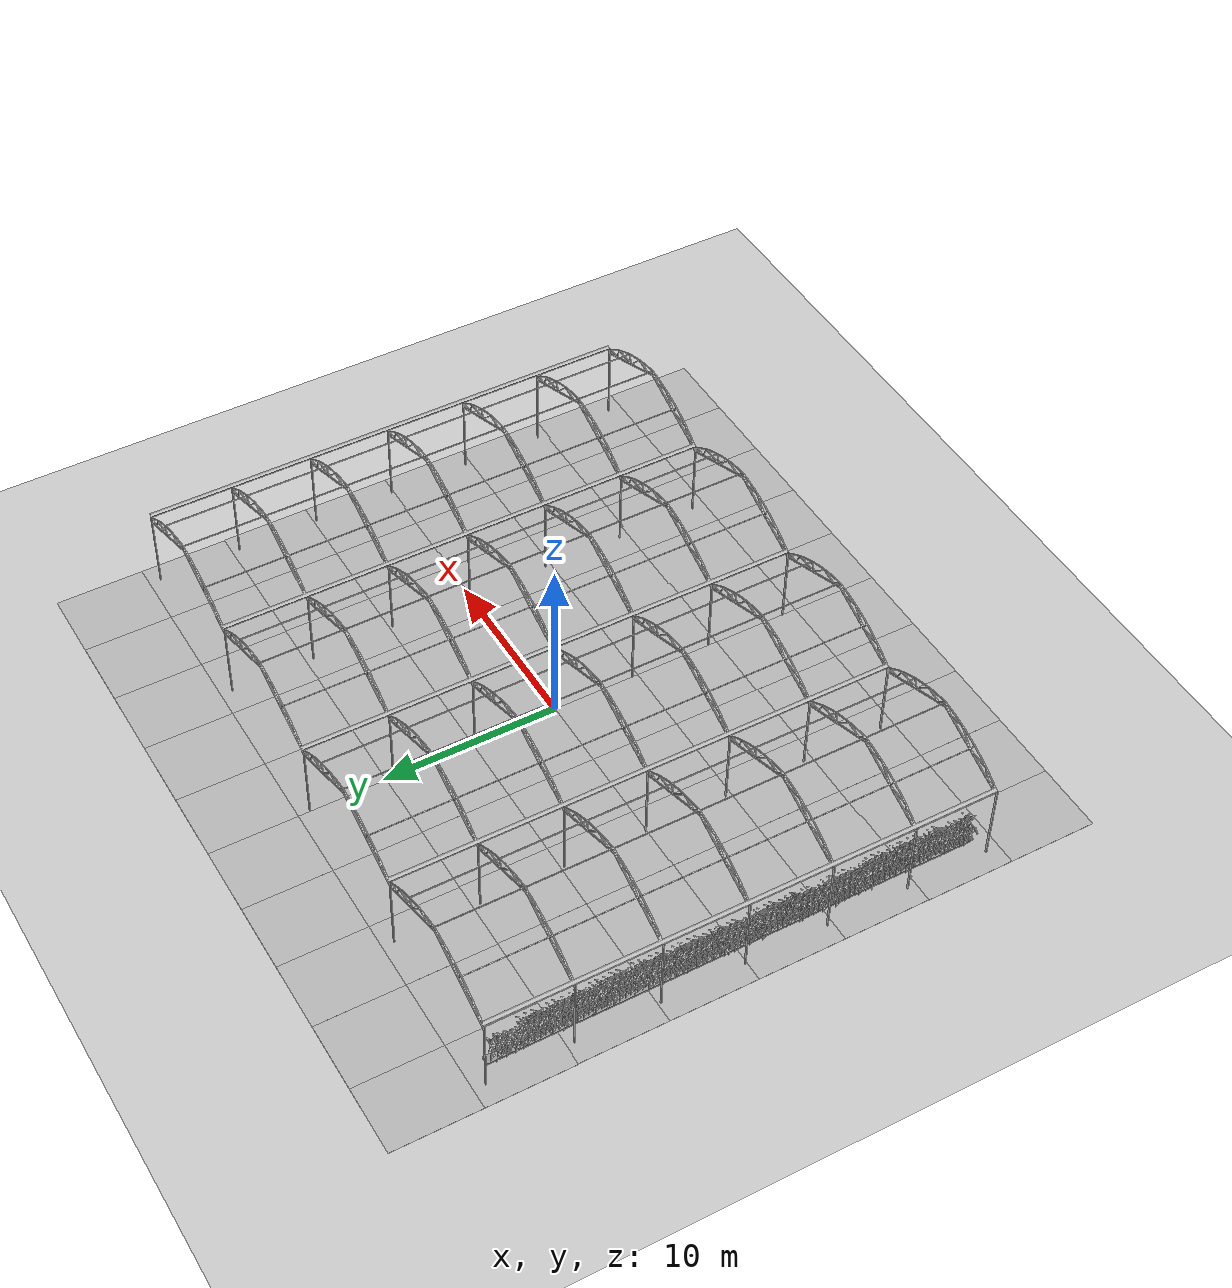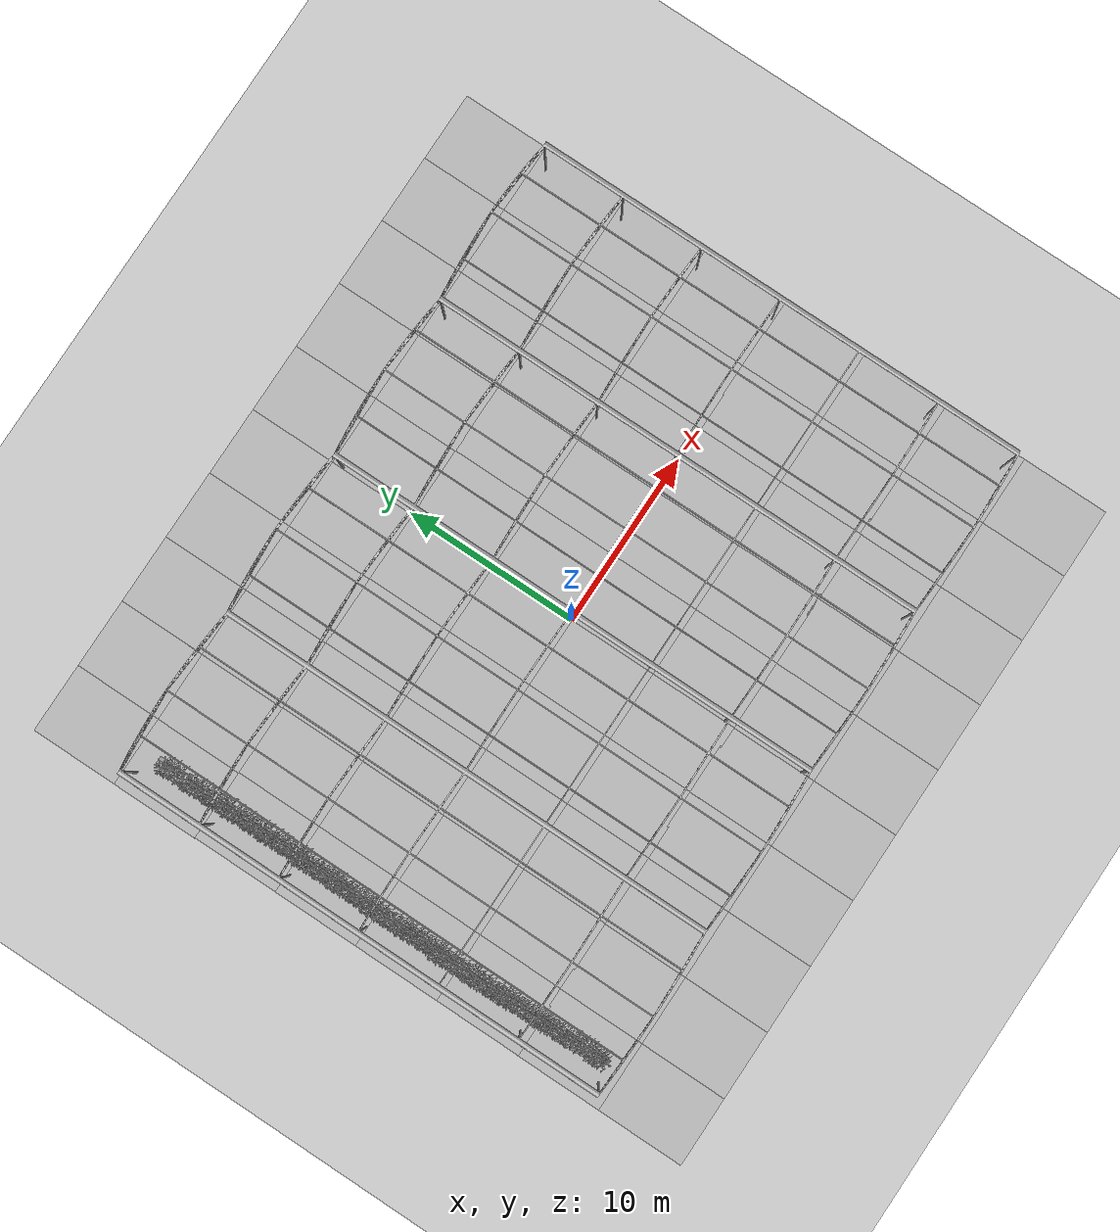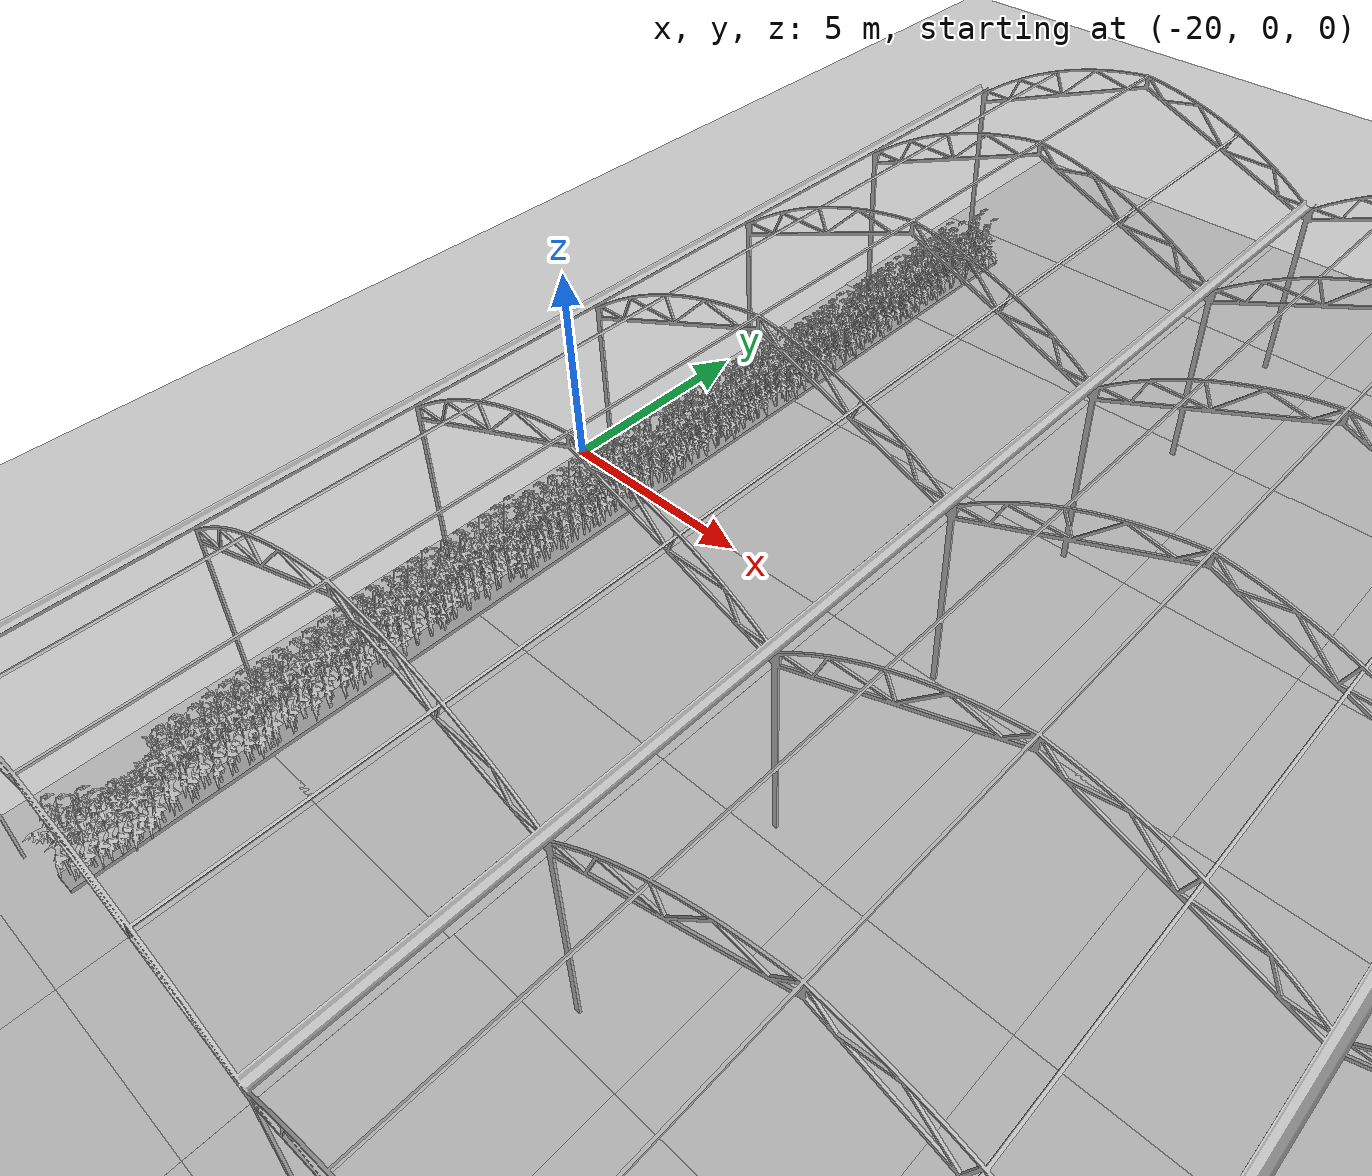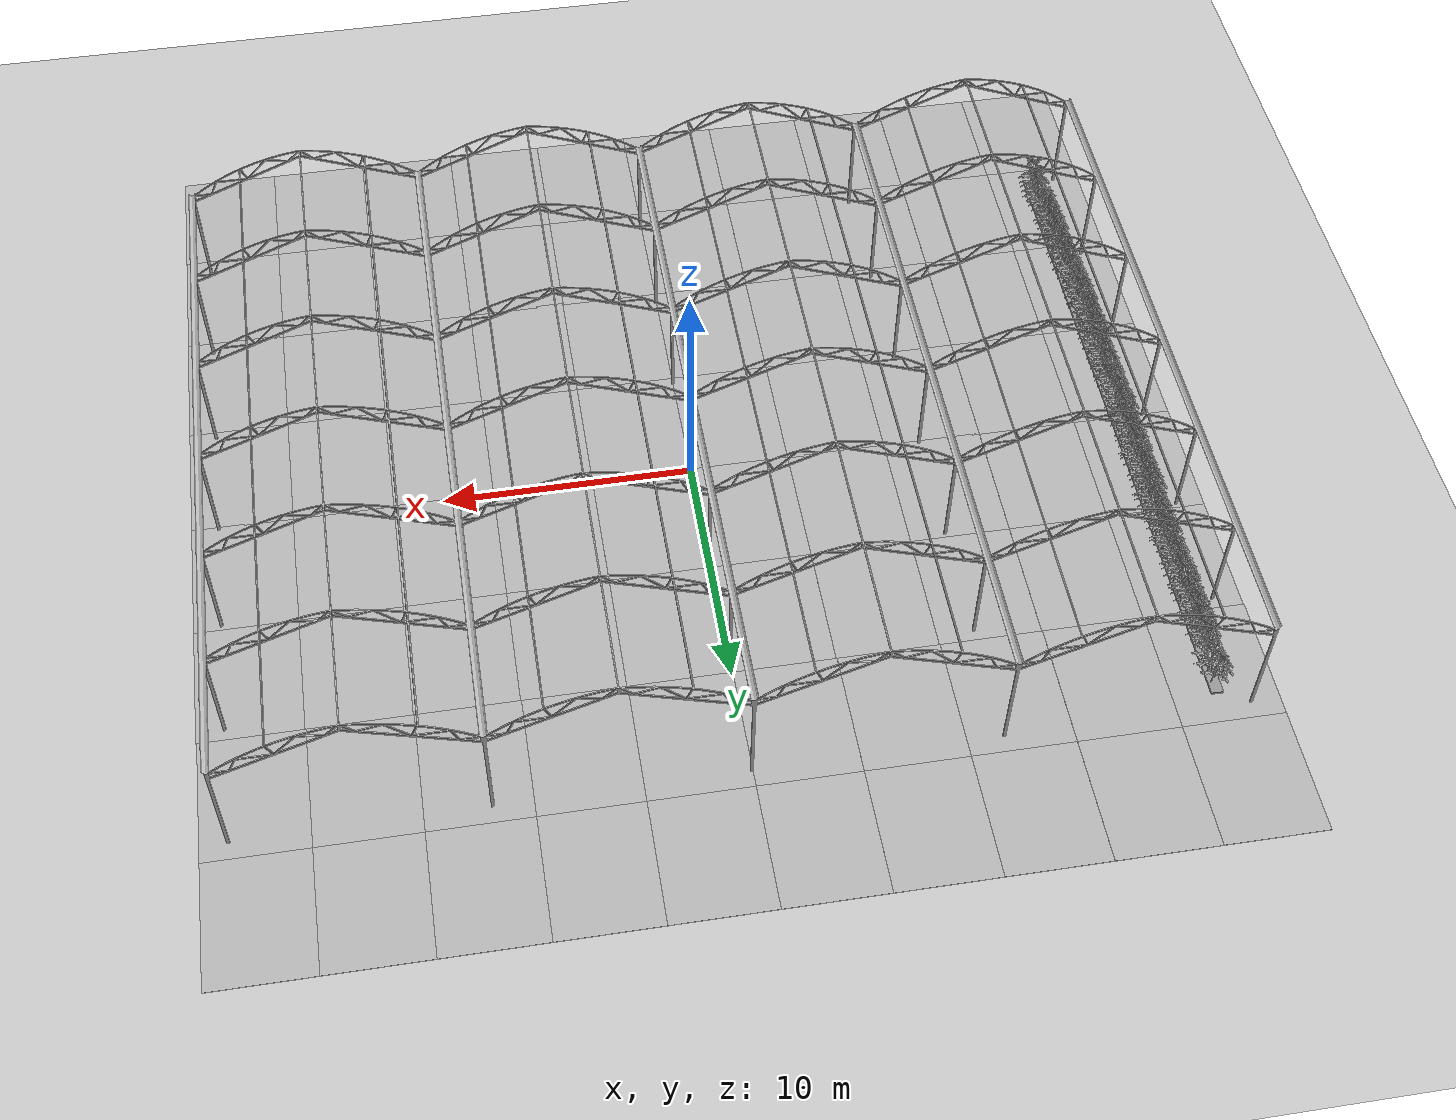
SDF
<sdf version="1.6">
 <world name="default">
  <light name="sun" type="directional">
   <pose>0 0 10 0 -0 0</pose>
   <diffuse>0.8 0.8 0.8 1</diffuse>
   <specular>0.2 0.2 0.2 1</specular>
   <attenuation>
    <range>1000</range>
    <constant>0.9</constant>
    <linear>0.01</linear>
    <quadratic>0.001</quadratic>
   </attenuation>
   <direction>-0.5 0.1 -0.9</direction>
  </light>
  <model name="ground_plane">
   <static>1</static>
   <link name="link">
    <collision name="collision">
     <geometry><plane><normal>0 0 1</normal><size>100 100</size></plane></geometry>
     <surface>
      <contact><collide_bitmask>65535</collide_bitmask></contact>
      <friction><ode><mu>100</mu><mu2>50</mu2></ode></friction>
     </surface>
    </collision>
    <visual name="visual">
     <cast_shadows>0</cast_shadows>
     <geometry><plane><normal>0 0 1</normal><size>100 100</size></plane></geometry>
     <material>
      <script><uri>file://media/materials/scripts/gazebo.material</uri><name>Gazebo/Grey</name></script>
     </material>
    </visual>
   </link>
  </model>
  <gravity>0 0 -9.8</gravity>
  <magnetic_field>6e-06 2.3e-05 -4.2e-05</magnetic_field>
  <atmosphere type="adiabatic"/>
  <physics name="default_physics" default="0" type="ode">
   <max_step_size>0.001</max_step_size>
   <real_time_factor>1</real_time_factor>
   <real_time_update_rate>1000</real_time_update_rate>
  </physics>
  <scene><ambient>0.4 0.4 0.4 1</ambient><background>0.7 0.7 0.7 1</background><shadows>1</shadows></scene>
  <audio><device>default</device></audio>
  <spherical_coordinates>
   <surface_model>EARTH_WGS84</surface_model>
   <latitude_deg>0</latitude_deg>
   <longitude_deg>0</longitude_deg>
   <elevation>0</elevation>
   <heading_deg>0</heading_deg>
  </spherical_coordinates>
  <model name="greenhouse">
   <static>1</static>
   <link name="link">
    <collision name="collision">
     <geometry>
      <mesh><scale>0.05 0.05 0.05</scale><uri>model://greenhouse/meshes/greenhouse.dae</uri></mesh>
     </geometry>
    </collision>
    <visual name="visual">
     <geometry>
      <mesh><scale>0.03 0.03 0.03</scale><uri>model://greenhouse/meshes/greenhouse.dae</uri></mesh>
     </geometry>
    </visual>
   </link>
   <pose>-24.6631 -23.579 0 0 -0 0</pose>
  </model>
  <model name="Ground_Soil">
   <model name="mud_box">
    <static>1</static>
    <link name="link">
     <collision name="collision"><geometry><box><size>8 10 0.02</size></box></geometry></collision>
     <visual name="visual_1">
      <pose>-2 2.5 0 0 -0 0</pose>
      <cast_shadows>0</cast_shadows>
      <geometry><box><size>4 5 0.02</size></box></geometry>
      <material>
       <script>
        <uri>model://mud_box/materials/scripts</uri>
        <uri>model://mud_box/materials/textures</uri>
        <name>vrc/mud</name>
       </script>
      </material>
     </visual>
     <visual name="visual_2">
      <pose>2 2.5 0 0 -0 0</pose>
      <cast_shadows>0</cast_shadows>
      <geometry><box><size>4 5 0.02</size></box></geometry>
      <material>
       <script>
        <uri>model://mud_box/materials/scripts</uri>
        <uri>model://mud_box/materials/textures</uri>
        <name>vrc/mud</name>
       </script>
      </material>
     </visual>
     <visual name="visual_3">
      <pose>2 -2.5 0 0 -0 0</pose>
      <cast_shadows>0</cast_shadows>
      <geometry><box><size>4 5 0.02</size></box></geometry>
      <material>
       <script>
        <uri>model://mud_box/materials/scripts</uri>
        <uri>model://mud_box/materials/textures</uri>
        <name>vrc/mud</name>
       </script>
      </material>
     </visual>
     <visual name="visual_4">
      <pose>-2 -2.5 0 0 -0 0</pose>
      <cast_shadows>0</cast_shadows>
      <geometry><box><size>4 5 0.02</size></box></geometry>
      <material>
       <script>
        <uri>model://mud_box/materials/scripts</uri>
        <uri>model://mud_box/materials/textures</uri>
        <name>vrc/mud</name>
       </script>
      </material>
     </visual>
    </link>
    <pose>-16.0013 0.000118 0 0 -0 0</pose>
   </model>
   <model name="mud_box_0">
    <static>1</static>
    <link name="link">
     <collision name="collision"><geometry><box><size>8 10 0.02</size></box></geometry></collision>
     <visual name="visual_1">
      <pose>-2 2.5 0 0 -0 0</pose>
      <cast_shadows>0</cast_shadows>
      <geometry><box><size>4 5 0.02</size></box></geometry>
      <material>
       <script>
        <uri>model://mud_box/materials/scripts</uri>
        <uri>model://mud_box/materials/textures</uri>
        <name>vrc/mud</name>
       </script>
      </material>
     </visual>
     <visual name="visual_2">
      <pose>2 2.5 0 0 -0 0</pose>
      <cast_shadows>0</cast_shadows>
      <geometry><box><size>4 5 0.02</size></box></geometry>
      <material>
       <script>
        <uri>model://mud_box/materials/scripts</uri>
        <uri>model://mud_box/materials/textures</uri>
        <name>vrc/mud</name>
       </script>
      </material>
     </visual>
     <visual name="visual_3">
      <pose>2 -2.5 0 0 -0 0</pose>
      <cast_shadows>0</cast_shadows>
      <geometry><box><size>4 5 0.02</size></box></geometry>
      <material>
       <script>
        <uri>model://mud_box/materials/scripts</uri>
        <uri>model://mud_box/materials/textures</uri>
        <name>vrc/mud</name>
       </script>
      </material>
     </visual>
     <visual name="visual_4">
      <pose>-2 -2.5 0 0 -0 0</pose>
      <cast_shadows>0</cast_shadows>
      <geometry><box><size>4 5 0.02</size></box></geometry>
      <material>
       <script>
        <uri>model://mud_box/materials/scripts</uri>
        <uri>model://mud_box/materials/textures</uri>
        <name>vrc/mud</name>
       </script>
      </material>
     </visual>
    </link>
    <pose>-7.99939 9.1e-05 0 0 -0 0</pose>
   </model>
   <model name="mud_box_1">
    <static>1</static>
    <link name="link">
     <collision name="collision"><geometry><box><size>8 10 0.02</size></box></geometry></collision>
     <visual name="visual_1">
      <pose>-2 2.5 0 0 -0 0</pose>
      <cast_shadows>0</cast_shadows>
      <geometry><box><size>4 5 0.02</size></box></geometry>
      <material>
       <script>
        <uri>model://mud_box/materials/scripts</uri>
        <uri>model://mud_box/materials/textures</uri>
        <name>vrc/mud</name>
       </script>
      </material>
     </visual>
     <visual name="visual_2">
      <pose>2 2.5 0 0 -0 0</pose>
      <cast_shadows>0</cast_shadows>
      <geometry><box><size>4 5 0.02</size></box></geometry>
      <material>
       <script>
        <uri>model://mud_box/materials/scripts</uri>
        <uri>model://mud_box/materials/textures</uri>
        <name>vrc/mud</name>
       </script>
      </material>
     </visual>
     <visual name="visual_3">
      <pose>2 -2.5 0 0 -0 0</pose>
      <cast_shadows>0</cast_shadows>
      <geometry><box><size>4 5 0.02</size></box></geometry>
      <material>
       <script>
        <uri>model://mud_box/materials/scripts</uri>
        <uri>model://mud_box/materials/textures</uri>
        <name>vrc/mud</name>
       </script>
      </material>
     </visual>
     <visual name="visual_4">
      <pose>-2 -2.5 0 0 -0 0</pose>
      <cast_shadows>0</cast_shadows>
      <geometry><box><size>4 5 0.02</size></box></geometry>
      <material>
       <script>
        <uri>model://mud_box/materials/scripts</uri>
        <uri>model://mud_box/materials/textures</uri>
        <name>vrc/mud</name>
       </script>
      </material>
     </visual>
    </link>
    <pose>0.000809 -0.000342 0 0 -0 0</pose>
   </model>
   <model name="mud_box_2">
    <static>1</static>
    <link name="link">
     <collision name="collision"><geometry><box><size>8 10 0.02</size></box></geometry></collision>
     <visual name="visual_1">
      <pose>-2 2.5 0 0 -0 0</pose>
      <cast_shadows>0</cast_shadows>
      <geometry><box><size>4 5 0.02</size></box></geometry>
      <material>
       <script>
        <uri>model://mud_box/materials/scripts</uri>
        <uri>model://mud_box/materials/textures</uri>
        <name>vrc/mud</name>
       </script>
      </material>
     </visual>
     <visual name="visual_2">
      <pose>2 2.5 0 0 -0 0</pose>
      <cast_shadows>0</cast_shadows>
      <geometry><box><size>4 5 0.02</size></box></geometry>
      <material>
       <script>
        <uri>model://mud_box/materials/scripts</uri>
        <uri>model://mud_box/materials/textures</uri>
        <name>vrc/mud</name>
       </script>
      </material>
     </visual>
     <visual name="visual_3">
      <pose>2 -2.5 0 0 -0 0</pose>
      <cast_shadows>0</cast_shadows>
      <geometry><box><size>4 5 0.02</size></box></geometry>
      <material>
       <script>
        <uri>model://mud_box/materials/scripts</uri>
        <uri>model://mud_box/materials/textures</uri>
        <name>vrc/mud</name>
       </script>
      </material>
     </visual>
     <visual name="visual_4">
      <pose>-2 -2.5 0 0 -0 0</pose>
      <cast_shadows>0</cast_shadows>
      <geometry><box><size>4 5 0.02</size></box></geometry>
      <material>
       <script>
        <uri>model://mud_box/materials/scripts</uri>
        <uri>model://mud_box/materials/textures</uri>
        <name>vrc/mud</name>
       </script>
      </material>
     </visual>
    </link>
    <pose>8.00089 -0.000148 0 0 -0 0</pose>
   </model>
   <model name="mud_box_3">
    <static>1</static>
    <link name="link">
     <collision name="collision"><geometry><box><size>8 10 0.02</size></box></geometry></collision>
     <visual name="visual_1">
      <pose>-2 2.5 0 0 -0 0</pose>
      <cast_shadows>0</cast_shadows>
      <geometry><box><size>4 5 0.02</size></box></geometry>
      <material>
       <script>
        <uri>model://mud_box/materials/scripts</uri>
        <uri>model://mud_box/materials/textures</uri>
        <name>vrc/mud</name>
       </script>
      </material>
     </visual>
     <visual name="visual_2">
      <pose>2 2.5 0 0 -0 0</pose>
      <cast_shadows>0</cast_shadows>
      <geometry><box><size>4 5 0.02</size></box></geometry>
      <material>
       <script>
        <uri>model://mud_box/materials/scripts</uri>
        <uri>model://mud_box/materials/textures</uri>
        <name>vrc/mud</name>
       </script>
      </material>
     </visual>
     <visual name="visual_3">
      <pose>2 -2.5 0 0 -0 0</pose>
      <cast_shadows>0</cast_shadows>
      <geometry><box><size>4 5 0.02</size></box></geometry>
      <material>
       <script>
        <uri>model://mud_box/materials/scripts</uri>
        <uri>model://mud_box/materials/textures</uri>
        <name>vrc/mud</name>
       </script>
      </material>
     </visual>
     <visual name="visual_4">
      <pose>-2 -2.5 0 0 -0 0</pose>
      <cast_shadows>0</cast_shadows>
      <geometry><box><size>4 5 0.02</size></box></geometry>
      <material>
       <script>
        <uri>model://mud_box/materials/scripts</uri>
        <uri>model://mud_box/materials/textures</uri>
        <name>vrc/mud</name>
       </script>
      </material>
     </visual>
    </link>
    <pose>15.9991 0.000313 0 0 -0 0</pose>
   </model>
   <static>0</static>
   <pose>-0.029393 -14.9577 0 0 -0 0</pose>
  </model>
  <model name="Ground_Soil_0">
   <model name="mud_box">
    <static>1</static>
    <link name="link">
     <collision name="collision"><geometry><box><size>8 10 0.02</size></box></geometry></collision>
     <visual name="visual_1">
      <pose>-2 2.5 0 0 -0 0</pose>
      <cast_shadows>0</cast_shadows>
      <geometry><box><size>4 5 0.02</size></box></geometry>
      <material>
       <script>
        <uri>model://mud_box/materials/scripts</uri>
        <uri>model://mud_box/materials/textures</uri>
        <name>vrc/mud</name>
       </script>
      </material>
     </visual>
     <visual name="visual_2">
      <pose>2 2.5 0 0 -0 0</pose>
      <cast_shadows>0</cast_shadows>
      <geometry><box><size>4 5 0.02</size></box></geometry>
      <material>
       <script>
        <uri>model://mud_box/materials/scripts</uri>
        <uri>model://mud_box/materials/textures</uri>
        <name>vrc/mud</name>
       </script>
      </material>
     </visual>
     <visual name="visual_3">
      <pose>2 -2.5 0 0 -0 0</pose>
      <cast_shadows>0</cast_shadows>
      <geometry><box><size>4 5 0.02</size></box></geometry>
      <material>
       <script>
        <uri>model://mud_box/materials/scripts</uri>
        <uri>model://mud_box/materials/textures</uri>
        <name>vrc/mud</name>
       </script>
      </material>
     </visual>
     <visual name="visual_4">
      <pose>-2 -2.5 0 0 -0 0</pose>
      <cast_shadows>0</cast_shadows>
      <geometry><box><size>4 5 0.02</size></box></geometry>
      <material>
       <script>
        <uri>model://mud_box/materials/scripts</uri>
        <uri>model://mud_box/materials/textures</uri>
        <name>vrc/mud</name>
       </script>
      </material>
     </visual>
    </link>
    <pose>-16.0013 0.000118 0 0 -0 0</pose>
   </model>
   <model name="mud_box_0">
    <static>1</static>
    <link name="link">
     <collision name="collision"><geometry><box><size>8 10 0.02</size></box></geometry></collision>
     <visual name="visual_1">
      <pose>-2 2.5 0 0 -0 0</pose>
      <cast_shadows>0</cast_shadows>
      <geometry><box><size>4 5 0.02</size></box></geometry>
      <material>
       <script>
        <uri>model://mud_box/materials/scripts</uri>
        <uri>model://mud_box/materials/textures</uri>
        <name>vrc/mud</name>
       </script>
      </material>
     </visual>
     <visual name="visual_2">
      <pose>2 2.5 0 0 -0 0</pose>
      <cast_shadows>0</cast_shadows>
      <geometry><box><size>4 5 0.02</size></box></geometry>
      <material>
       <script>
        <uri>model://mud_box/materials/scripts</uri>
        <uri>model://mud_box/materials/textures</uri>
        <name>vrc/mud</name>
       </script>
      </material>
     </visual>
     <visual name="visual_3">
      <pose>2 -2.5 0 0 -0 0</pose>
      <cast_shadows>0</cast_shadows>
      <geometry><box><size>4 5 0.02</size></box></geometry>
      <material>
       <script>
        <uri>model://mud_box/materials/scripts</uri>
        <uri>model://mud_box/materials/textures</uri>
        <name>vrc/mud</name>
       </script>
      </material>
     </visual>
     <visual name="visual_4">
      <pose>-2 -2.5 0 0 -0 0</pose>
      <cast_shadows>0</cast_shadows>
      <geometry><box><size>4 5 0.02</size></box></geometry>
      <material>
       <script>
        <uri>model://mud_box/materials/scripts</uri>
        <uri>model://mud_box/materials/textures</uri>
        <name>vrc/mud</name>
       </script>
      </material>
     </visual>
    </link>
    <pose>-7.99939 9.1e-05 0 0 -0 0</pose>
   </model>
   <model name="mud_box_1">
    <static>1</static>
    <link name="link">
     <collision name="collision"><geometry><box><size>8 10 0.02</size></box></geometry></collision>
     <visual name="visual_1">
      <pose>-2 2.5 0 0 -0 0</pose>
      <cast_shadows>0</cast_shadows>
      <geometry><box><size>4 5 0.02</size></box></geometry>
      <material>
       <script>
        <uri>model://mud_box/materials/scripts</uri>
        <uri>model://mud_box/materials/textures</uri>
        <name>vrc/mud</name>
       </script>
      </material>
     </visual>
     <visual name="visual_2">
      <pose>2 2.5 0 0 -0 0</pose>
      <cast_shadows>0</cast_shadows>
      <geometry><box><size>4 5 0.02</size></box></geometry>
      <material>
       <script>
        <uri>model://mud_box/materials/scripts</uri>
        <uri>model://mud_box/materials/textures</uri>
        <name>vrc/mud</name>
       </script>
      </material>
     </visual>
     <visual name="visual_3">
      <pose>2 -2.5 0 0 -0 0</pose>
      <cast_shadows>0</cast_shadows>
      <geometry><box><size>4 5 0.02</size></box></geometry>
      <material>
       <script>
        <uri>model://mud_box/materials/scripts</uri>
        <uri>model://mud_box/materials/textures</uri>
        <name>vrc/mud</name>
       </script>
      </material>
     </visual>
     <visual name="visual_4">
      <pose>-2 -2.5 0 0 -0 0</pose>
      <cast_shadows>0</cast_shadows>
      <geometry><box><size>4 5 0.02</size></box></geometry>
      <material>
       <script>
        <uri>model://mud_box/materials/scripts</uri>
        <uri>model://mud_box/materials/textures</uri>
        <name>vrc/mud</name>
       </script>
      </material>
     </visual>
    </link>
    <pose>0.000809 -0.000342 0 0 -0 0</pose>
   </model>
   <model name="mud_box_2">
    <static>1</static>
    <link name="link">
     <collision name="collision"><geometry><box><size>8 10 0.02</size></box></geometry></collision>
     <visual name="visual_1">
      <pose>-2 2.5 0 0 -0 0</pose>
      <cast_shadows>0</cast_shadows>
      <geometry><box><size>4 5 0.02</size></box></geometry>
      <material>
       <script>
        <uri>model://mud_box/materials/scripts</uri>
        <uri>model://mud_box/materials/textures</uri>
        <name>vrc/mud</name>
       </script>
      </material>
     </visual>
     <visual name="visual_2">
      <pose>2 2.5 0 0 -0 0</pose>
      <cast_shadows>0</cast_shadows>
      <geometry><box><size>4 5 0.02</size></box></geometry>
      <material>
       <script>
        <uri>model://mud_box/materials/scripts</uri>
        <uri>model://mud_box/materials/textures</uri>
        <name>vrc/mud</name>
       </script>
      </material>
     </visual>
     <visual name="visual_3">
      <pose>2 -2.5 0 0 -0 0</pose>
      <cast_shadows>0</cast_shadows>
      <geometry><box><size>4 5 0.02</size></box></geometry>
      <material>
       <script>
        <uri>model://mud_box/materials/scripts</uri>
        <uri>model://mud_box/materials/textures</uri>
        <name>vrc/mud</name>
       </script>
      </material>
     </visual>
     <visual name="visual_4">
      <pose>-2 -2.5 0 0 -0 0</pose>
      <cast_shadows>0</cast_shadows>
      <geometry><box><size>4 5 0.02</size></box></geometry>
      <material>
       <script>
        <uri>model://mud_box/materials/scripts</uri>
        <uri>model://mud_box/materials/textures</uri>
        <name>vrc/mud</name>
       </script>
      </material>
     </visual>
    </link>
    <pose>8.00089 -0.000148 0 0 -0 0</pose>
   </model>
   <model name="mud_box_3">
    <static>1</static>
    <link name="link">
     <collision name="collision"><geometry><box><size>8 10 0.02</size></box></geometry></collision>
     <visual name="visual_1">
      <pose>-2 2.5 0 0 -0 0</pose>
      <cast_shadows>0</cast_shadows>
      <geometry><box><size>4 5 0.02</size></box></geometry>
      <material>
       <script>
        <uri>model://mud_box/materials/scripts</uri>
        <uri>model://mud_box/materials/textures</uri>
        <name>vrc/mud</name>
       </script>
      </material>
     </visual>
     <visual name="visual_2">
      <pose>2 2.5 0 0 -0 0</pose>
      <cast_shadows>0</cast_shadows>
      <geometry><box><size>4 5 0.02</size></box></geometry>
      <material>
       <script>
        <uri>model://mud_box/materials/scripts</uri>
        <uri>model://mud_box/materials/textures</uri>
        <name>vrc/mud</name>
       </script>
      </material>
     </visual>
     <visual name="visual_3">
      <pose>2 -2.5 0 0 -0 0</pose>
      <cast_shadows>0</cast_shadows>
      <geometry><box><size>4 5 0.02</size></box></geometry>
      <material>
       <script>
        <uri>model://mud_box/materials/scripts</uri>
        <uri>model://mud_box/materials/textures</uri>
        <name>vrc/mud</name>
       </script>
      </material>
     </visual>
     <visual name="visual_4">
      <pose>-2 -2.5 0 0 -0 0</pose>
      <cast_shadows>0</cast_shadows>
      <geometry><box><size>4 5 0.02</size></box></geometry>
      <material>
       <script>
        <uri>model://mud_box/materials/scripts</uri>
        <uri>model://mud_box/materials/textures</uri>
        <name>vrc/mud</name>
       </script>
      </material>
     </visual>
    </link>
    <pose>15.9991 0.000313 0 0 -0 0</pose>
   </model>
   <static>0</static>
   <pose>-0.0126 -5.05002 0 0 -0 0</pose>
  </model>
  <model name="Ground_Soil_1">
   <model name="mud_box">
    <static>1</static>
    <link name="link">
     <collision name="collision"><geometry><box><size>8 10 0.02</size></box></geometry></collision>
     <visual name="visual_1">
      <pose>-2 2.5 0 0 -0 0</pose>
      <cast_shadows>0</cast_shadows>
      <geometry><box><size>4 5 0.02</size></box></geometry>
      <material>
       <script>
        <uri>model://mud_box/materials/scripts</uri>
        <uri>model://mud_box/materials/textures</uri>
        <name>vrc/mud</name>
       </script>
      </material>
     </visual>
     <visual name="visual_2">
      <pose>2 2.5 0 0 -0 0</pose>
      <cast_shadows>0</cast_shadows>
      <geometry><box><size>4 5 0.02</size></box></geometry>
      <material>
       <script>
        <uri>model://mud_box/materials/scripts</uri>
        <uri>model://mud_box/materials/textures</uri>
        <name>vrc/mud</name>
       </script>
      </material>
     </visual>
     <visual name="visual_3">
      <pose>2 -2.5 0 0 -0 0</pose>
      <cast_shadows>0</cast_shadows>
      <geometry><box><size>4 5 0.02</size></box></geometry>
      <material>
       <script>
        <uri>model://mud_box/materials/scripts</uri>
        <uri>model://mud_box/materials/textures</uri>
        <name>vrc/mud</name>
       </script>
      </material>
     </visual>
     <visual name="visual_4">
      <pose>-2 -2.5 0 0 -0 0</pose>
      <cast_shadows>0</cast_shadows>
      <geometry><box><size>4 5 0.02</size></box></geometry>
      <material>
       <script>
        <uri>model://mud_box/materials/scripts</uri>
        <uri>model://mud_box/materials/textures</uri>
        <name>vrc/mud</name>
       </script>
      </material>
     </visual>
    </link>
    <pose>-16.0013 0.000118 0 0 -0 0</pose>
   </model>
   <model name="mud_box_0">
    <static>1</static>
    <link name="link">
     <collision name="collision"><geometry><box><size>8 10 0.02</size></box></geometry></collision>
     <visual name="visual_1">
      <pose>-2 2.5 0 0 -0 0</pose>
      <cast_shadows>0</cast_shadows>
      <geometry><box><size>4 5 0.02</size></box></geometry>
      <material>
       <script>
        <uri>model://mud_box/materials/scripts</uri>
        <uri>model://mud_box/materials/textures</uri>
        <name>vrc/mud</name>
       </script>
      </material>
     </visual>
     <visual name="visual_2">
      <pose>2 2.5 0 0 -0 0</pose>
      <cast_shadows>0</cast_shadows>
      <geometry><box><size>4 5 0.02</size></box></geometry>
      <material>
       <script>
        <uri>model://mud_box/materials/scripts</uri>
        <uri>model://mud_box/materials/textures</uri>
        <name>vrc/mud</name>
       </script>
      </material>
     </visual>
     <visual name="visual_3">
      <pose>2 -2.5 0 0 -0 0</pose>
      <cast_shadows>0</cast_shadows>
      <geometry><box><size>4 5 0.02</size></box></geometry>
      <material>
       <script>
        <uri>model://mud_box/materials/scripts</uri>
        <uri>model://mud_box/materials/textures</uri>
        <name>vrc/mud</name>
       </script>
      </material>
     </visual>
     <visual name="visual_4">
      <pose>-2 -2.5 0 0 -0 0</pose>
      <cast_shadows>0</cast_shadows>
      <geometry><box><size>4 5 0.02</size></box></geometry>
      <material>
       <script>
        <uri>model://mud_box/materials/scripts</uri>
        <uri>model://mud_box/materials/textures</uri>
        <name>vrc/mud</name>
       </script>
      </material>
     </visual>
    </link>
    <pose>-7.99939 9.1e-05 0 0 -0 0</pose>
   </model>
   <model name="mud_box_1">
    <static>1</static>
    <link name="link">
     <collision name="collision"><geometry><box><size>8 10 0.02</size></box></geometry></collision>
     <visual name="visual_1">
      <pose>-2 2.5 0 0 -0 0</pose>
      <cast_shadows>0</cast_shadows>
      <geometry><box><size>4 5 0.02</size></box></geometry>
      <material>
       <script>
        <uri>model://mud_box/materials/scripts</uri>
        <uri>model://mud_box/materials/textures</uri>
        <name>vrc/mud</name>
       </script>
      </material>
     </visual>
     <visual name="visual_2">
      <pose>2 2.5 0 0 -0 0</pose>
      <cast_shadows>0</cast_shadows>
      <geometry><box><size>4 5 0.02</size></box></geometry>
      <material>
       <script>
        <uri>model://mud_box/materials/scripts</uri>
        <uri>model://mud_box/materials/textures</uri>
        <name>vrc/mud</name>
       </script>
      </material>
     </visual>
     <visual name="visual_3">
      <pose>2 -2.5 0 0 -0 0</pose>
      <cast_shadows>0</cast_shadows>
      <geometry><box><size>4 5 0.02</size></box></geometry>
      <material>
       <script>
        <uri>model://mud_box/materials/scripts</uri>
        <uri>model://mud_box/materials/textures</uri>
        <name>vrc/mud</name>
       </script>
      </material>
     </visual>
     <visual name="visual_4">
      <pose>-2 -2.5 0 0 -0 0</pose>
      <cast_shadows>0</cast_shadows>
      <geometry><box><size>4 5 0.02</size></box></geometry>
      <material>
       <script>
        <uri>model://mud_box/materials/scripts</uri>
        <uri>model://mud_box/materials/textures</uri>
        <name>vrc/mud</name>
       </script>
      </material>
     </visual>
    </link>
    <pose>0.000809 -0.000342 0 0 -0 0</pose>
   </model>
   <model name="mud_box_2">
    <static>1</static>
    <link name="link">
     <collision name="collision"><geometry><box><size>8 10 0.02</size></box></geometry></collision>
     <visual name="visual_1">
      <pose>-2 2.5 0 0 -0 0</pose>
      <cast_shadows>0</cast_shadows>
      <geometry><box><size>4 5 0.02</size></box></geometry>
      <material>
       <script>
        <uri>model://mud_box/materials/scripts</uri>
        <uri>model://mud_box/materials/textures</uri>
        <name>vrc/mud</name>
       </script>
      </material>
     </visual>
     <visual name="visual_2">
      <pose>2 2.5 0 0 -0 0</pose>
      <cast_shadows>0</cast_shadows>
      <geometry><box><size>4 5 0.02</size></box></geometry>
      <material>
       <script>
        <uri>model://mud_box/materials/scripts</uri>
        <uri>model://mud_box/materials/textures</uri>
        <name>vrc/mud</name>
       </script>
      </material>
     </visual>
     <visual name="visual_3">
      <pose>2 -2.5 0 0 -0 0</pose>
      <cast_shadows>0</cast_shadows>
      <geometry><box><size>4 5 0.02</size></box></geometry>
      <material>
       <script>
        <uri>model://mud_box/materials/scripts</uri>
        <uri>model://mud_box/materials/textures</uri>
        <name>vrc/mud</name>
       </script>
      </material>
     </visual>
     <visual name="visual_4">
      <pose>-2 -2.5 0 0 -0 0</pose>
      <cast_shadows>0</cast_shadows>
      <geometry><box><size>4 5 0.02</size></box></geometry>
      <material>
       <script>
        <uri>model://mud_box/materials/scripts</uri>
        <uri>model://mud_box/materials/textures</uri>
        <name>vrc/mud</name>
       </script>
      </material>
     </visual>
    </link>
    <pose>8.00089 -0.000148 0 0 -0 0</pose>
   </model>
   <model name="mud_box_3">
    <static>1</static>
    <link name="link">
     <collision name="collision"><geometry><box><size>8 10 0.02</size></box></geometry></collision>
     <visual name="visual_1">
      <pose>-2 2.5 0 0 -0 0</pose>
      <cast_shadows>0</cast_shadows>
      <geometry><box><size>4 5 0.02</size></box></geometry>
      <material>
       <script>
        <uri>model://mud_box/materials/scripts</uri>
        <uri>model://mud_box/materials/textures</uri>
        <name>vrc/mud</name>
       </script>
      </material>
     </visual>
     <visual name="visual_2">
      <pose>2 2.5 0 0 -0 0</pose>
      <cast_shadows>0</cast_shadows>
      <geometry><box><size>4 5 0.02</size></box></geometry>
      <material>
       <script>
        <uri>model://mud_box/materials/scripts</uri>
        <uri>model://mud_box/materials/textures</uri>
        <name>vrc/mud</name>
       </script>
      </material>
     </visual>
     <visual name="visual_3">
      <pose>2 -2.5 0 0 -0 0</pose>
      <cast_shadows>0</cast_shadows>
      <geometry><box><size>4 5 0.02</size></box></geometry>
      <material>
       <script>
        <uri>model://mud_box/materials/scripts</uri>
        <uri>model://mud_box/materials/textures</uri>
        <name>vrc/mud</name>
       </script>
      </material>
     </visual>
     <visual name="visual_4">
      <pose>-2 -2.5 0 0 -0 0</pose>
      <cast_shadows>0</cast_shadows>
      <geometry><box><size>4 5 0.02</size></box></geometry>
      <material>
       <script>
        <uri>model://mud_box/materials/scripts</uri>
        <uri>model://mud_box/materials/textures</uri>
        <name>vrc/mud</name>
       </script>
      </material>
     </visual>
    </link>
    <pose>15.9991 0.000313 0 0 -0 0</pose>
   </model>
   <static>0</static>
   <pose>-0.0126 4.89814 0 0 -0 0</pose>
  </model>
  <model name="Ground_Soil_2">
   <model name="mud_box">
    <static>1</static>
    <link name="link">
     <collision name="collision"><geometry><box><size>8 10 0.02</size></box></geometry></collision>
     <visual name="visual_1">
      <pose>-2 2.5 0 0 -0 0</pose>
      <cast_shadows>0</cast_shadows>
      <geometry><box><size>4 5 0.02</size></box></geometry>
      <material>
       <script>
        <uri>model://mud_box/materials/scripts</uri>
        <uri>model://mud_box/materials/textures</uri>
        <name>vrc/mud</name>
       </script>
      </material>
     </visual>
     <visual name="visual_2">
      <pose>2 2.5 0 0 -0 0</pose>
      <cast_shadows>0</cast_shadows>
      <geometry><box><size>4 5 0.02</size></box></geometry>
      <material>
       <script>
        <uri>model://mud_box/materials/scripts</uri>
        <uri>model://mud_box/materials/textures</uri>
        <name>vrc/mud</name>
       </script>
      </material>
     </visual>
     <visual name="visual_3">
      <pose>2 -2.5 0 0 -0 0</pose>
      <cast_shadows>0</cast_shadows>
      <geometry><box><size>4 5 0.02</size></box></geometry>
      <material>
       <script>
        <uri>model://mud_box/materials/scripts</uri>
        <uri>model://mud_box/materials/textures</uri>
        <name>vrc/mud</name>
       </script>
      </material>
     </visual>
     <visual name="visual_4">
      <pose>-2 -2.5 0 0 -0 0</pose>
      <cast_shadows>0</cast_shadows>
      <geometry><box><size>4 5 0.02</size></box></geometry>
      <material>
       <script>
        <uri>model://mud_box/materials/scripts</uri>
        <uri>model://mud_box/materials/textures</uri>
        <name>vrc/mud</name>
       </script>
      </material>
     </visual>
    </link>
    <pose>-16.0013 0.000118 0 0 -0 0</pose>
   </model>
   <model name="mud_box_0">
    <static>1</static>
    <link name="link">
     <collision name="collision"><geometry><box><size>8 10 0.02</size></box></geometry></collision>
     <visual name="visual_1">
      <pose>-2 2.5 0 0 -0 0</pose>
      <cast_shadows>0</cast_shadows>
      <geometry><box><size>4 5 0.02</size></box></geometry>
      <material>
       <script>
        <uri>model://mud_box/materials/scripts</uri>
        <uri>model://mud_box/materials/textures</uri>
        <name>vrc/mud</name>
       </script>
      </material>
     </visual>
     <visual name="visual_2">
      <pose>2 2.5 0 0 -0 0</pose>
      <cast_shadows>0</cast_shadows>
      <geometry><box><size>4 5 0.02</size></box></geometry>
      <material>
       <script>
        <uri>model://mud_box/materials/scripts</uri>
        <uri>model://mud_box/materials/textures</uri>
        <name>vrc/mud</name>
       </script>
      </material>
     </visual>
     <visual name="visual_3">
      <pose>2 -2.5 0 0 -0 0</pose>
      <cast_shadows>0</cast_shadows>
      <geometry><box><size>4 5 0.02</size></box></geometry>
      <material>
       <script>
        <uri>model://mud_box/materials/scripts</uri>
        <uri>model://mud_box/materials/textures</uri>
        <name>vrc/mud</name>
       </script>
      </material>
     </visual>
     <visual name="visual_4">
      <pose>-2 -2.5 0 0 -0 0</pose>
      <cast_shadows>0</cast_shadows>
      <geometry><box><size>4 5 0.02</size></box></geometry>
      <material>
       <script>
        <uri>model://mud_box/materials/scripts</uri>
        <uri>model://mud_box/materials/textures</uri>
        <name>vrc/mud</name>
       </script>
      </material>
     </visual>
    </link>
    <pose>-7.99939 9.1e-05 0 0 -0 0</pose>
   </model>
   <model name="mud_box_1">
    <static>1</static>
    <link name="link">
     <collision name="collision"><geometry><box><size>8 10 0.02</size></box></geometry></collision>
     <visual name="visual_1">
      <pose>-2 2.5 0 0 -0 0</pose>
      <cast_shadows>0</cast_shadows>
      <geometry><box><size>4 5 0.02</size></box></geometry>
      <material>
       <script>
        <uri>model://mud_box/materials/scripts</uri>
        <uri>model://mud_box/materials/textures</uri>
        <name>vrc/mud</name>
       </script>
      </material>
     </visual>
     <visual name="visual_2">
      <pose>2 2.5 0 0 -0 0</pose>
      <cast_shadows>0</cast_shadows>
      <geometry><box><size>4 5 0.02</size></box></geometry>
      <material>
       <script>
        <uri>model://mud_box/materials/scripts</uri>
        <uri>model://mud_box/materials/textures</uri>
        <name>vrc/mud</name>
       </script>
      </material>
     </visual>
     <visual name="visual_3">
      <pose>2 -2.5 0 0 -0 0</pose>
      <cast_shadows>0</cast_shadows>
      <geometry><box><size>4 5 0.02</size></box></geometry>
      <material>
       <script>
        <uri>model://mud_box/materials/scripts</uri>
        <uri>model://mud_box/materials/textures</uri>
        <name>vrc/mud</name>
       </script>
      </material>
     </visual>
     <visual name="visual_4">
      <pose>-2 -2.5 0 0 -0 0</pose>
      <cast_shadows>0</cast_shadows>
      <geometry><box><size>4 5 0.02</size></box></geometry>
      <material>
       <script>
        <uri>model://mud_box/materials/scripts</uri>
        <uri>model://mud_box/materials/textures</uri>
        <name>vrc/mud</name>
       </script>
      </material>
     </visual>
    </link>
    <pose>0.000809 -0.000342 0 0 -0 0</pose>
   </model>
   <model name="mud_box_2">
    <static>1</static>
    <link name="link">
     <collision name="collision"><geometry><box><size>8 10 0.02</size></box></geometry></collision>
     <visual name="visual_1">
      <pose>-2 2.5 0 0 -0 0</pose>
      <cast_shadows>0</cast_shadows>
      <geometry><box><size>4 5 0.02</size></box></geometry>
      <material>
       <script>
        <uri>model://mud_box/materials/scripts</uri>
        <uri>model://mud_box/materials/textures</uri>
        <name>vrc/mud</name>
       </script>
      </material>
     </visual>
     <visual name="visual_2">
      <pose>2 2.5 0 0 -0 0</pose>
      <cast_shadows>0</cast_shadows>
      <geometry><box><size>4 5 0.02</size></box></geometry>
      <material>
       <script>
        <uri>model://mud_box/materials/scripts</uri>
        <uri>model://mud_box/materials/textures</uri>
        <name>vrc/mud</name>
       </script>
      </material>
     </visual>
     <visual name="visual_3">
      <pose>2 -2.5 0 0 -0 0</pose>
      <cast_shadows>0</cast_shadows>
      <geometry><box><size>4 5 0.02</size></box></geometry>
      <material>
       <script>
        <uri>model://mud_box/materials/scripts</uri>
        <uri>model://mud_box/materials/textures</uri>
        <name>vrc/mud</name>
       </script>
      </material>
     </visual>
     <visual name="visual_4">
      <pose>-2 -2.5 0 0 -0 0</pose>
      <cast_shadows>0</cast_shadows>
      <geometry><box><size>4 5 0.02</size></box></geometry>
      <material>
       <script>
        <uri>model://mud_box/materials/scripts</uri>
        <uri>model://mud_box/materials/textures</uri>
        <name>vrc/mud</name>
       </script>
      </material>
     </visual>
    </link>
    <pose>8.00089 -0.000148 0 0 -0 0</pose>
   </model>
   <model name="mud_box_3">
    <static>1</static>
    <link name="link">
     <collision name="collision"><geometry><box><size>8 10 0.02</size></box></geometry></collision>
     <visual name="visual_1">
      <pose>-2 2.5 0 0 -0 0</pose>
      <cast_shadows>0</cast_shadows>
      <geometry><box><size>4 5 0.02</size></box></geometry>
      <material>
       <script>
        <uri>model://mud_box/materials/scripts</uri>
        <uri>model://mud_box/materials/textures</uri>
        <name>vrc/mud</name>
       </script>
      </material>
     </visual>
     <visual name="visual_2">
      <pose>2 2.5 0 0 -0 0</pose>
      <cast_shadows>0</cast_shadows>
      <geometry><box><size>4 5 0.02</size></box></geometry>
      <material>
       <script>
        <uri>model://mud_box/materials/scripts</uri>
        <uri>model://mud_box/materials/textures</uri>
        <name>vrc/mud</name>
       </script>
      </material>
     </visual>
     <visual name="visual_3">
      <pose>2 -2.5 0 0 -0 0</pose>
      <cast_shadows>0</cast_shadows>
      <geometry><box><size>4 5 0.02</size></box></geometry>
      <material>
       <script>
        <uri>model://mud_box/materials/scripts</uri>
        <uri>model://mud_box/materials/textures</uri>
        <name>vrc/mud</name>
       </script>
      </material>
     </visual>
     <visual name="visual_4">
      <pose>-2 -2.5 0 0 -0 0</pose>
      <cast_shadows>0</cast_shadows>
      <geometry><box><size>4 5 0.02</size></box></geometry>
      <material>
       <script>
        <uri>model://mud_box/materials/scripts</uri>
        <uri>model://mud_box/materials/textures</uri>
        <name>vrc/mud</name>
       </script>
      </material>
     </visual>
    </link>
    <pose>15.9991 0.000313 0 0 -0 0</pose>
   </model>
   <static>0</static>
   <pose>-0.0462 14.8693 0 0 -0 0</pose>
  </model>
  <model name="Front_Plant">
   <model name="Front_Plant">
    <model name="Front_Plant">
     <model name="tomato_plant_big">
      <static>1</static>
      <link name="link">
       <collision name="collision">
        <geometry>
         <mesh><scale>5e-06 5e-06 6e-06</scale><uri>model://tomato_plant_big/meshes/tomato-plant.dae</uri></mesh>
        </geometry>
       </collision>
       <visual name="visual">
        <geometry>
         <mesh><scale>5e-06 5e-06 7e-06</scale><uri>model://tomato_plant_big/meshes/tomato-plant.dae</uri></mesh>
        </geometry>
       </visual>
      </link>
      <pose>0.066099 -0.5693 0 0 -0 0</pose>
     </model>
     <model name="tomato_plant_big_0">
      <static>1</static>
      <link name="link">
       <collision name="collision">
        <geometry>
         <mesh><scale>5e-06 5e-06 6e-06</scale><uri>model://tomato_plant_big/meshes/tomato-plant.dae</uri></mesh>
        </geometry>
       </collision>
       <visual name="visual">
        <geometry>
         <mesh><scale>5e-06 5e-06 7e-06</scale><uri>model://tomato_plant_big/meshes/tomato-plant.dae</uri></mesh>
        </geometry>
       </visual>
      </link>
      <pose>-0.127857 -0.732187 0 0 -0 0</pose>
     </model>
     <model name="tomato_plant_medium">
      <static>1</static>
      <link name="link">
       <collision name="collision">
        <geometry>
         <mesh><scale>5e-06 5e-06 6e-06</scale><uri>model://tomato_plant_medium/meshes/tomato-plant.dae</uri></mesh>
        </geometry>
       </collision>
       <visual name="visual">
        <geometry>
         <mesh><scale>5e-06 5e-06 6e-06</scale><uri>model://tomato_plant_medium/meshes/tomato-plant.dae</uri></mesh>
        </geometry>
       </visual>
      </link>
      <pose>0.122987 0.218142 0 0 -0 0</pose>
     </model>
     <model name="tomato_plant_medium_0">
      <static>1</static>
      <link name="link">
       <collision name="collision">
        <geometry>
         <mesh><scale>5e-06 5e-06 6e-06</scale><uri>model://tomato_plant_medium/meshes/tomato-plant.dae</uri></mesh>
        </geometry>
       </collision>
       <visual name="visual">
        <geometry>
         <mesh><scale>5e-06 5e-06 6e-06</scale><uri>model://tomato_plant_medium/meshes/tomato-plant.dae</uri></mesh>
        </geometry>
       </visual>
      </link>
      <pose>0.063601 -0.11224 0 0 -0 0</pose>
     </model>
     <model name="tomato_plant_medium_1">
      <static>1</static>
      <link name="link">
       <collision name="collision">
        <geometry>
         <mesh><scale>5e-06 5e-06 6e-06</scale><uri>model://tomato_plant_medium/meshes/tomato-plant.dae</uri></mesh>
        </geometry>
       </collision>
       <visual name="visual">
        <geometry>
         <mesh><scale>5e-06 5e-06 6e-06</scale><uri>model://tomato_plant_medium/meshes/tomato-plant.dae</uri></mesh>
        </geometry>
       </visual>
      </link>
      <pose>-0.136409 -0.201165 0 0 -0 0</pose>
     </model>
     <model name="tomato_plant_medium_2">
      <static>1</static>
      <link name="link">
       <collision name="collision">
        <geometry>
         <mesh><scale>5e-06 5e-06 6e-06</scale><uri>model://tomato_plant_medium/meshes/tomato-plant.dae</uri></mesh>
        </geometry>
       </collision>
       <visual name="visual">
        <geometry>
         <mesh><scale>5e-06 5e-06 6e-06</scale><uri>model://tomato_plant_medium/meshes/tomato-plant.dae</uri></mesh>
        </geometry>
       </visual>
      </link>
      <pose>0.058749 -0.366518 0 0 -0 0</pose>
     </model>
     <model name="tomato_plant_small">
      <static>1</static>
      <link name="link">
       <collision name="collision">
        <geometry>
         <mesh><scale>5e-06 5e-06 5e-06</scale><uri>model://tomato_plant_small/meshes/tomato-plant.dae</uri></mesh>
        </geometry>
       </collision>
       <visual name="visual">
        <geometry>
         <mesh><scale>5e-06 5e-06 5e-06</scale><uri>model://tomato_plant_small/meshes/tomato-plant.dae</uri></mesh>
        </geometry>
       </visual>
      </link>
      <pose>-0.070714 0.646602 0 0 -0 0</pose>
     </model>
     <model name="tomato_plant_small_0">
      <static>1</static>
      <link name="link">
       <collision name="collision">
        <geometry>
         <mesh><scale>5e-06 5e-06 5e-06</scale><uri>model://tomato_plant_small/meshes/tomato-plant.dae</uri></mesh>
        </geometry>
       </collision>
       <visual name="visual">
        <geometry>
         <mesh><scale>5e-06 5e-06 5e-06</scale><uri>model://tomato_plant_small/meshes/tomato-plant.dae</uri></mesh>
        </geometry>
       </visual>
      </link>
      <pose>0.074729 0.75209 0 0 -0 0</pose>
     </model>
     <model name="tomato_plant_small_1">
      <static>1</static>
      <link name="link">
       <collision name="collision">
        <geometry>
         <mesh><scale>5e-06 5e-06 5e-06</scale><uri>model://tomato_plant_small/meshes/tomato-plant.dae</uri></mesh>
        </geometry>
       </collision>
       <visual name="visual">
        <geometry>
         <mesh><scale>5e-06 5e-06 5e-06</scale><uri>model://tomato_plant_small/meshes/tomato-plant.dae</uri></mesh>
        </geometry>
       </visual>
      </link>
      <pose>0.12147 0.444739 0 0 -0 0</pose>
     </model>
     <model name="tomato_plant_small_2">
      <static>1</static>
      <link name="link">
       <collision name="collision">
        <geometry>
         <mesh><scale>5e-06 5e-06 5e-06</scale><uri>model://tomato_plant_small/meshes/tomato-plant.dae</uri></mesh>
        </geometry>
       </collision>
       <visual name="visual">
        <geometry>
         <mesh><scale>5e-06 5e-06 5e-06</scale><uri>model://tomato_plant_small/meshes/tomato-plant.dae</uri></mesh>
        </geometry>
       </visual>
      </link>
      <pose>-0.041969 0.348263 0 0 -0 0</pose>
     </model>
     <model name="tomato_plant_small_3">
      <static>1</static>
      <link name="link">
       <collision name="collision">
        <geometry>
         <mesh><scale>5e-06 5e-06 5e-06</scale><uri>model://tomato_plant_small/meshes/tomato-plant.dae</uri></mesh>
        </geometry>
       </collision>
       <visual name="visual">
        <geometry>
         <mesh><scale>5e-06 5e-06 5e-06</scale><uri>model://tomato_plant_small/meshes/tomato-plant.dae</uri></mesh>
        </geometry>
       </visual>
      </link>
      <pose>-0.0217 0.061756 0 0 -0 0</pose>
     </model>
     <model name="tomato_plant_small_4">
      <static>1</static>
      <link name="link">
       <collision name="collision">
        <geometry>
         <mesh><scale>5e-06 5e-06 5e-06</scale><uri>model://tomato_plant_small/meshes/tomato-plant.dae</uri></mesh>
        </geometry>
       </collision>
       <visual name="visual">
        <geometry>
         <mesh><scale>5e-06 5e-06 5e-06</scale><uri>model://tomato_plant_small/meshes/tomato-plant.dae</uri></mesh>
        </geometry>
       </visual>
      </link>
      <pose>-0.108883 -0.490262 0 0 -0 0</pose>
     </model>
     <static>0</static>
     <pose>0.012031 -0.967708 0 0 -0 0</pose>
    </model>
    <model name="Middle_Plant">
     <model name="tomato_plant_big">
      <static>1</static>
      <link name="link">
       <collision name="collision">
        <geometry>
         <mesh><scale>5e-06 5e-06 6e-06</scale><uri>model://tomato_plant_big/meshes/tomato-plant.dae</uri></mesh>
        </geometry>
       </collision>
       <visual name="visual">
        <geometry>
         <mesh><scale>5e-06 5e-06 7e-06</scale><uri>model://tomato_plant_big/meshes/tomato-plant.dae</uri></mesh>
        </geometry>
       </visual>
      </link>
      <pose>0.085326 1.23023 0 0 -0 0</pose>
     </model>
     <model name="tomato_plant_big_0">
      <static>1</static>
      <link name="link">
       <collision name="collision">
        <geometry>
         <mesh><scale>5e-06 5e-06 6e-06</scale><uri>model://tomato_plant_big/meshes/tomato-plant.dae</uri></mesh>
        </geometry>
       </collision>
       <visual name="visual">
        <geometry>
         <mesh><scale>5e-06 5e-06 7e-06</scale><uri>model://tomato_plant_big/meshes/tomato-plant.dae</uri></mesh>
        </geometry>
       </visual>
      </link>
      <pose>-0.133881 0.970183 0 0 -0 0</pose>
     </model>
     <model name="tomato_plant_big_1">
      <static>1</static>
      <link name="link">
       <collision name="collision">
        <geometry>
         <mesh><scale>5e-06 5e-06 6e-06</scale><uri>model://tomato_plant_big/meshes/tomato-plant.dae</uri></mesh>
        </geometry>
       </collision>
       <visual name="visual">
        <geometry>
         <mesh><scale>5e-06 5e-06 7e-06</scale><uri>model://tomato_plant_big/meshes/tomato-plant.dae</uri></mesh>
        </geometry>
       </visual>
      </link>
      <pose>0.091162 0.792381 0 0 -0 0</pose>
     </model>
     <model name="tomato_plant_big_2">
      <static>1</static>
      <link name="link">
       <collision name="collision">
        <geometry>
         <mesh><scale>5e-06 5e-06 6e-06</scale><uri>model://tomato_plant_big/meshes/tomato-plant.dae</uri></mesh>
        </geometry>
       </collision>
       <visual name="visual">
        <geometry>
         <mesh><scale>5e-06 5e-06 7e-06</scale><uri>model://tomato_plant_big/meshes/tomato-plant.dae</uri></mesh>
        </geometry>
       </visual>
      </link>
      <pose>-0.099228 0.602587 0 0 -0 0</pose>
     </model>
     <model name="tomato_plant_big_3">
      <static>1</static>
      <link name="link">
       <collision name="collision">
        <geometry>
         <mesh><scale>5e-06 5e-06 6e-06</scale><uri>model://tomato_plant_big/meshes/tomato-plant.dae</uri></mesh>
        </geometry>
       </collision>
       <visual name="visual">
        <geometry>
         <mesh><scale>5e-06 5e-06 7e-06</scale><uri>model://tomato_plant_big/meshes/tomato-plant.dae</uri></mesh>
        </geometry>
       </visual>
      </link>
      <pose>0.083199 0.447645 0 0 -0 0</pose>
     </model>
     <model name="tomato_plant_big_4">
      <static>1</static>
      <link name="link">
       <collision name="collision">
        <geometry>
         <mesh><scale>5e-06 5e-06 6e-06</scale><uri>model://tomato_plant_big/meshes/tomato-plant.dae</uri></mesh>
        </geometry>
       </collision>
       <visual name="visual">
        <geometry>
         <mesh><scale>5e-06 5e-06 7e-06</scale><uri>model://tomato_plant_big/meshes/tomato-plant.dae</uri></mesh>
        </geometry>
       </visual>
      </link>
      <pose>-0.079499 0.263486 0 0 -0 0</pose>
     </model>
     <model name="tomato_plant_big_5">
      <static>1</static>
      <link name="link">
       <collision name="collision">
        <geometry>
         <mesh><scale>5e-06 5e-06 6e-06</scale><uri>model://tomato_plant_big/meshes/tomato-plant.dae</uri></mesh>
        </geometry>
       </collision>
       <visual name="visual">
        <geometry>
         <mesh><scale>5e-06 5e-06 7e-06</scale><uri>model://tomato_plant_big/meshes/tomato-plant.dae</uri></mesh>
        </geometry>
       </visual>
      </link>
      <pose>-0.033274 -0.040578 0 0 -0 0</pose>
     </model>
     <model name="tomato_plant_big_6">
      <static>1</static>
      <link name="link">
       <collision name="collision">
        <geometry>
         <mesh><scale>5e-06 5e-06 6e-06</scale><uri>model://tomato_plant_big/meshes/tomato-plant.dae</uri></mesh>
        </geometry>
       </collision>
       <visual name="visual">
        <geometry>
         <mesh><scale>5e-06 5e-06 7e-06</scale><uri>model://tomato_plant_big/meshes/tomato-plant.dae</uri></mesh>
        </geometry>
       </visual>
      </link>
      <pose>-0.07669 -0.382406 0 0 -0 0</pose>
     </model>
     <model name="tomato_plant_big_7">
      <static>1</static>
      <link name="link">
       <collision name="collision">
        <geometry>
         <mesh><scale>5e-06 5e-06 6e-06</scale><uri>model://tomato_plant_big/meshes/tomato-plant.dae</uri></mesh>
        </geometry>
       </collision>
       <visual name="visual">
        <geometry>
         <mesh><scale>5e-06 5e-06 7e-06</scale><uri>model://tomato_plant_big/meshes/tomato-plant.dae</uri></mesh>
        </geometry>
       </visual>
      </link>
      <pose>0.092388 -0.348189 0 0 -0 0</pose>
     </model>
     <model name="tomato_plant_big_8">
      <static>1</static>
      <link name="link">
       <collision name="collision">
        <geometry>
         <mesh><scale>5e-06 5e-06 6e-06</scale><uri>model://tomato_plant_big/meshes/tomato-plant.dae</uri></mesh>
        </geometry>
       </collision>
       <visual name="visual">
        <geometry>
         <mesh><scale>5e-06 5e-06 7e-06</scale><uri>model://tomato_plant_big/meshes/tomato-plant.dae</uri></mesh>
        </geometry>
       </visual>
      </link>
      <pose>0.099522 -0.697525 0 0 -0 0</pose>
     </model>
     <model name="tomato_plant_big_9">
      <static>1</static>
      <link name="link">
       <collision name="collision">
        <geometry>
         <mesh><scale>5e-06 5e-06 6e-06</scale><uri>model://tomato_plant_big/meshes/tomato-plant.dae</uri></mesh>
        </geometry>
       </collision>
       <visual name="visual">
        <geometry>
         <mesh><scale>5e-06 5e-06 7e-06</scale><uri>model://tomato_plant_big/meshes/tomato-plant.dae</uri></mesh>
        </geometry>
       </visual>
      </link>
      <pose>-0.050449 -0.712772 0 0 -0 0</pose>
     </model>
     <model name="tomato_plant_medium">
      <static>1</static>
      <link name="link">
       <collision name="collision">
        <geometry>
         <mesh><scale>5e-06 5e-06 6e-06</scale><uri>model://tomato_plant_medium/meshes/tomato-plant.dae</uri></mesh>
        </geometry>
       </collision>
       <visual name="visual">
        <geometry>
         <mesh><scale>5e-06 5e-06 6e-06</scale><uri>model://tomato_plant_medium/meshes/tomato-plant.dae</uri></mesh>
        </geometry>
       </visual>
      </link>
      <pose>0.078434 0.139842 0 0 -0 0</pose>
     </model>
     <model name="tomato_plant_medium_0">
      <static>1</static>
      <link name="link">
       <collision name="collision">
        <geometry>
         <mesh><scale>5e-06 5e-06 6e-06</scale><uri>model://tomato_plant_medium/meshes/tomato-plant.dae</uri></mesh>
        </geometry>
       </collision>
       <visual name="visual">
        <geometry>
         <mesh><scale>5e-06 5e-06 6e-06</scale><uri>model://tomato_plant_medium/meshes/tomato-plant.dae</uri></mesh>
        </geometry>
       </visual>
      </link>
      <pose>-0.079755 -0.244483 0 0 -0 0</pose>
     </model>
     <model name="tomato_plant_medium_1">
      <static>1</static>
      <link name="link">
       <collision name="collision">
        <geometry>
         <mesh><scale>5e-06 5e-06 6e-06</scale><uri>model://tomato_plant_medium/meshes/tomato-plant.dae</uri></mesh>
        </geometry>
       </collision>
       <visual name="visual">
        <geometry>
         <mesh><scale>5e-06 5e-06 6e-06</scale><uri>model://tomato_plant_medium/meshes/tomato-plant.dae</uri></mesh>
        </geometry>
       </visual>
      </link>
      <pose>0.106744 -1.01815 0 0 -0 0</pose>
     </model>
     <model name="tomato_plant_small">
      <static>1</static>
      <link name="link">
       <collision name="collision">
        <geometry>
         <mesh><scale>5e-06 5e-06 5e-06</scale><uri>model://tomato_plant_small/meshes/tomato-plant.dae</uri></mesh>
        </geometry>
       </collision>
       <visual name="visual">
        <geometry>
         <mesh><scale>5e-06 5e-06 5e-06</scale><uri>model://tomato_plant_small/meshes/tomato-plant.dae</uri></mesh>
        </geometry>
       </visual>
      </link>
      <pose>-0.083979 -1.00222 0 0 -0 0</pose>
     </model>
     <static>0</static>
     <pose>-0.012038 0.96777 0 0 -0 0</pose>
    </model>
    <static>0</static>
    <pose>0.018711 -1.52253 0 0 -0 0</pose>
   </model>
   <model name="Middle_Plant">
    <model name="tomato_plant_big">
     <static>1</static>
     <link name="link">
      <collision name="collision">
       <geometry>
        <mesh><scale>5e-06 5e-06 6e-06</scale><uri>model://tomato_plant_big/meshes/tomato-plant.dae</uri></mesh>
       </geometry>
      </collision>
      <visual name="visual">
       <geometry>
        <mesh><scale>5e-06 5e-06 7e-06</scale><uri>model://tomato_plant_big/meshes/tomato-plant.dae</uri></mesh>
       </geometry>
      </visual>
     </link>
     <pose>0.085326 1.23023 0 0 -0 0</pose>
    </model>
    <model name="tomato_plant_big_0">
     <static>1</static>
     <link name="link">
      <collision name="collision">
       <geometry>
        <mesh><scale>5e-06 5e-06 6e-06</scale><uri>model://tomato_plant_big/meshes/tomato-plant.dae</uri></mesh>
       </geometry>
      </collision>
      <visual name="visual">
       <geometry>
        <mesh><scale>5e-06 5e-06 7e-06</scale><uri>model://tomato_plant_big/meshes/tomato-plant.dae</uri></mesh>
       </geometry>
      </visual>
     </link>
     <pose>-0.133881 0.970183 0 0 -0 0</pose>
    </model>
    <model name="tomato_plant_big_1">
     <static>1</static>
     <link name="link">
      <collision name="collision">
       <geometry>
        <mesh><scale>5e-06 5e-06 6e-06</scale><uri>model://tomato_plant_big/meshes/tomato-plant.dae</uri></mesh>
       </geometry>
      </collision>
      <visual name="visual">
       <geometry>
        <mesh><scale>5e-06 5e-06 7e-06</scale><uri>model://tomato_plant_big/meshes/tomato-plant.dae</uri></mesh>
       </geometry>
      </visual>
     </link>
     <pose>0.091162 0.792381 0 0 -0 0</pose>
    </model>
    <model name="tomato_plant_big_2">
     <static>1</static>
     <link name="link">
      <collision name="collision">
       <geometry>
        <mesh><scale>5e-06 5e-06 6e-06</scale><uri>model://tomato_plant_big/meshes/tomato-plant.dae</uri></mesh>
       </geometry>
      </collision>
      <visual name="visual">
       <geometry>
        <mesh><scale>5e-06 5e-06 7e-06</scale><uri>model://tomato_plant_big/meshes/tomato-plant.dae</uri></mesh>
       </geometry>
      </visual>
     </link>
     <pose>-0.099228 0.602587 0 0 -0 0</pose>
    </model>
    <model name="tomato_plant_big_3">
     <static>1</static>
     <link name="link">
      <collision name="collision">
       <geometry>
        <mesh><scale>5e-06 5e-06 6e-06</scale><uri>model://tomato_plant_big/meshes/tomato-plant.dae</uri></mesh>
       </geometry>
      </collision>
      <visual name="visual">
       <geometry>
        <mesh><scale>5e-06 5e-06 7e-06</scale><uri>model://tomato_plant_big/meshes/tomato-plant.dae</uri></mesh>
       </geometry>
      </visual>
     </link>
     <pose>0.083199 0.447645 0 0 -0 0</pose>
    </model>
    <model name="tomato_plant_big_4">
     <static>1</static>
     <link name="link">
      <collision name="collision">
       <geometry>
        <mesh><scale>5e-06 5e-06 6e-06</scale><uri>model://tomato_plant_big/meshes/tomato-plant.dae</uri></mesh>
       </geometry>
      </collision>
      <visual name="visual">
       <geometry>
        <mesh><scale>5e-06 5e-06 7e-06</scale><uri>model://tomato_plant_big/meshes/tomato-plant.dae</uri></mesh>
       </geometry>
      </visual>
     </link>
     <pose>-0.079499 0.263486 0 0 -0 0</pose>
    </model>
    <model name="tomato_plant_big_5">
     <static>1</static>
     <link name="link">
      <collision name="collision">
       <geometry>
        <mesh><scale>5e-06 5e-06 6e-06</scale><uri>model://tomato_plant_big/meshes/tomato-plant.dae</uri></mesh>
       </geometry>
      </collision>
      <visual name="visual">
       <geometry>
        <mesh><scale>5e-06 5e-06 7e-06</scale><uri>model://tomato_plant_big/meshes/tomato-plant.dae</uri></mesh>
       </geometry>
      </visual>
     </link>
     <pose>-0.033274 -0.040578 0 0 -0 0</pose>
    </model>
    <model name="tomato_plant_big_6">
     <static>1</static>
     <link name="link">
      <collision name="collision">
       <geometry>
        <mesh><scale>5e-06 5e-06 6e-06</scale><uri>model://tomato_plant_big/meshes/tomato-plant.dae</uri></mesh>
       </geometry>
      </collision>
      <visual name="visual">
       <geometry>
        <mesh><scale>5e-06 5e-06 7e-06</scale><uri>model://tomato_plant_big/meshes/tomato-plant.dae</uri></mesh>
       </geometry>
      </visual>
     </link>
     <pose>-0.07669 -0.382406 0 0 -0 0</pose>
    </model>
    <model name="tomato_plant_big_7">
     <static>1</static>
     <link name="link">
      <collision name="collision">
       <geometry>
        <mesh><scale>5e-06 5e-06 6e-06</scale><uri>model://tomato_plant_big/meshes/tomato-plant.dae</uri></mesh>
       </geometry>
      </collision>
      <visual name="visual">
       <geometry>
        <mesh><scale>5e-06 5e-06 7e-06</scale><uri>model://tomato_plant_big/meshes/tomato-plant.dae</uri></mesh>
       </geometry>
      </visual>
     </link>
     <pose>0.092388 -0.348189 0 0 -0 0</pose>
    </model>
    <model name="tomato_plant_big_8">
     <static>1</static>
     <link name="link">
      <collision name="collision">
       <geometry>
        <mesh><scale>5e-06 5e-06 6e-06</scale><uri>model://tomato_plant_big/meshes/tomato-plant.dae</uri></mesh>
       </geometry>
      </collision>
      <visual name="visual">
       <geometry>
        <mesh><scale>5e-06 5e-06 7e-06</scale><uri>model://tomato_plant_big/meshes/tomato-plant.dae</uri></mesh>
       </geometry>
      </visual>
     </link>
     <pose>0.099522 -0.697525 0 0 -0 0</pose>
    </model>
    <model name="tomato_plant_big_9">
     <static>1</static>
     <link name="link">
      <collision name="collision">
       <geometry>
        <mesh><scale>5e-06 5e-06 6e-06</scale><uri>model://tomato_plant_big/meshes/tomato-plant.dae</uri></mesh>
       </geometry>
      </collision>
      <visual name="visual">
       <geometry>
        <mesh><scale>5e-06 5e-06 7e-06</scale><uri>model://tomato_plant_big/meshes/tomato-plant.dae</uri></mesh>
       </geometry>
      </visual>
     </link>
     <pose>-0.050449 -0.712772 0 0 -0 0</pose>
    </model>
    <model name="tomato_plant_medium">
     <static>1</static>
     <link name="link">
      <collision name="collision">
       <geometry>
        <mesh><scale>5e-06 5e-06 6e-06</scale><uri>model://tomato_plant_medium/meshes/tomato-plant.dae</uri></mesh>
       </geometry>
      </collision>
      <visual name="visual">
       <geometry>
        <mesh><scale>5e-06 5e-06 6e-06</scale><uri>model://tomato_plant_medium/meshes/tomato-plant.dae</uri></mesh>
       </geometry>
      </visual>
     </link>
     <pose>0.078434 0.139842 0 0 -0 0</pose>
    </model>
    <model name="tomato_plant_medium_0">
     <static>1</static>
     <link name="link">
      <collision name="collision">
       <geometry>
        <mesh><scale>5e-06 5e-06 6e-06</scale><uri>model://tomato_plant_medium/meshes/tomato-plant.dae</uri></mesh>
       </geometry>
      </collision>
      <visual name="visual">
       <geometry>
        <mesh><scale>5e-06 5e-06 6e-06</scale><uri>model://tomato_plant_medium/meshes/tomato-plant.dae</uri></mesh>
       </geometry>
      </visual>
     </link>
     <pose>-0.079755 -0.244483 0 0 -0 0</pose>
    </model>
    <model name="tomato_plant_medium_1">
     <static>1</static>
     <link name="link">
      <collision name="collision">
       <geometry>
        <mesh><scale>5e-06 5e-06 6e-06</scale><uri>model://tomato_plant_medium/meshes/tomato-plant.dae</uri></mesh>
       </geometry>
      </collision>
      <visual name="visual">
       <geometry>
        <mesh><scale>5e-06 5e-06 6e-06</scale><uri>model://tomato_plant_medium/meshes/tomato-plant.dae</uri></mesh>
       </geometry>
      </visual>
     </link>
     <pose>0.106744 -1.01815 0 0 -0 0</pose>
    </model>
    <model name="tomato_plant_small">
     <static>1</static>
     <link name="link">
      <collision name="collision">
       <geometry>
        <mesh><scale>5e-06 5e-06 5e-06</scale><uri>model://tomato_plant_small/meshes/tomato-plant.dae</uri></mesh>
       </geometry>
      </collision>
      <visual name="visual">
       <geometry>
        <mesh><scale>5e-06 5e-06 5e-06</scale><uri>model://tomato_plant_small/meshes/tomato-plant.dae</uri></mesh>
       </geometry>
      </visual>
     </link>
     <pose>-0.083979 -1.00222 0 0 -0 0</pose>
    </model>
    <static>0</static>
    <pose>-0.018694 1.5225 0 0 -0 0</pose>
   </model>
   <static>0</static>
   <pose>-17.739 -10.5679 0 0 -0 0</pose>
  </model>
  <model name="Plant_Base_0">
   <model name="Plant_Base">
    <link name="link_0">
     <inertial>
      <mass>1.1839</mass>
      <inertia>
       <ixx>75.2086</ixx>
       <ixy>0</ixy>
       <ixz>0</ixz>
       <iyy>0.0226752</iyy>
       <iyz>0</iyz>
       <izz>75.2297</izz>
      </inertia>
     </inertial>
     <pose>1.3e-05 0 0 0 -0.006723 0</pose>
     <visual name="visual">
      <geometry><box><size>0.470639 27.6098 0.091294</size></box></geometry>
      <material>
       <lighting>1</lighting>
       <script><uri>file://media/materials/scripts/gazebo.material</uri><name>Gazebo/Grey</name></script>
      </material>
     </visual>
     <collision name="collision">
      <geometry><box><size>0.470639 27.6098 0.091294</size></box></geometry>
      <surface>
       <friction>
        <ode><mu>1</mu><mu2>1</mu2><fdir1>0 0 0</fdir1><slip1>0</slip1><slip2>0</slip2></ode>
        <torsional>
         <coefficient>1</coefficient>
         <patch_radius>0</patch_radius>
         <surface_radius>0</surface_radius>
         <use_patch_radius>1</use_patch_radius>
         <ode><slip>0</slip></ode>
        </torsional>
       </friction>
       <bounce><restitution_coefficient>0</restitution_coefficient><threshold>1e+06</threshold></bounce>
       <contact>
        <collide_without_contact>0</collide_without_contact>
        <collide_without_contact_bitmask>1</collide_without_contact_bitmask>
        <collide_bitmask>1</collide_bitmask>
        <ode>
         <soft_cfm>0</soft_cfm>
         <soft_erp>0.2</soft_erp>
         <kp>1e+13</kp>
         <kd>1</kd>
         <max_vel>0.01</max_vel>
         <min_depth>0</min_depth>
        </ode>
        <bullet>
         <split_impulse>1</split_impulse>
         <split_impulse_penetration_threshold>-0.01</split_impulse_penetration_threshold>
         <soft_cfm>0</soft_cfm>
         <soft_erp>0.2</soft_erp>
         <kp>1e+13</kp>
         <kd>1</kd>
        </bullet>
       </contact>
      </surface>
     </collision>
    </link>
    <static>0</static>
    <pose>-3.5e-05 3e-06 0 0 -0 0</pose>
   </model>
   <static>1</static>
   <pose>-17.7667 -0.137203 0.055519 0 -0 0</pose>
  </model>
  <model name="Middle_Plant_0">
   <model name="tomato_plant_big">
    <static>1</static>
    <link name="link">
     <collision name="collision">
      <geometry>
       <mesh><scale>5e-06 5e-06 6e-06</scale><uri>model://tomato_plant_big/meshes/tomato-plant.dae</uri></mesh>
      </geometry>
     </collision>
     <visual name="visual">
      <geometry>
       <mesh><scale>5e-06 5e-06 7e-06</scale><uri>model://tomato_plant_big/meshes/tomato-plant.dae</uri></mesh>
      </geometry>
     </visual>
    </link>
    <pose>0.085326 1.23023 0 0 -0 0</pose>
   </model>
   <model name="tomato_plant_big_0">
    <static>1</static>
    <link name="link">
     <collision name="collision">
      <geometry>
       <mesh><scale>5e-06 5e-06 6e-06</scale><uri>model://tomato_plant_big/meshes/tomato-plant.dae</uri></mesh>
      </geometry>
     </collision>
     <visual name="visual">
      <geometry>
       <mesh><scale>5e-06 5e-06 7e-06</scale><uri>model://tomato_plant_big/meshes/tomato-plant.dae</uri></mesh>
      </geometry>
     </visual>
    </link>
    <pose>-0.133881 0.970183 0 0 -0 0</pose>
   </model>
   <model name="tomato_plant_big_1">
    <static>1</static>
    <link name="link">
     <collision name="collision">
      <geometry>
       <mesh><scale>5e-06 5e-06 6e-06</scale><uri>model://tomato_plant_big/meshes/tomato-plant.dae</uri></mesh>
      </geometry>
     </collision>
     <visual name="visual">
      <geometry>
       <mesh><scale>5e-06 5e-06 7e-06</scale><uri>model://tomato_plant_big/meshes/tomato-plant.dae</uri></mesh>
      </geometry>
     </visual>
    </link>
    <pose>0.091162 0.792381 0 0 -0 0</pose>
   </model>
   <model name="tomato_plant_big_2">
    <static>1</static>
    <link name="link">
     <collision name="collision">
      <geometry>
       <mesh><scale>5e-06 5e-06 6e-06</scale><uri>model://tomato_plant_big/meshes/tomato-plant.dae</uri></mesh>
      </geometry>
     </collision>
     <visual name="visual">
      <geometry>
       <mesh><scale>5e-06 5e-06 7e-06</scale><uri>model://tomato_plant_big/meshes/tomato-plant.dae</uri></mesh>
      </geometry>
     </visual>
    </link>
    <pose>-0.099228 0.602587 0 0 -0 0</pose>
   </model>
   <model name="tomato_plant_big_3">
    <static>1</static>
    <link name="link">
     <collision name="collision">
      <geometry>
       <mesh><scale>5e-06 5e-06 6e-06</scale><uri>model://tomato_plant_big/meshes/tomato-plant.dae</uri></mesh>
      </geometry>
     </collision>
     <visual name="visual">
      <geometry>
       <mesh><scale>5e-06 5e-06 7e-06</scale><uri>model://tomato_plant_big/meshes/tomato-plant.dae</uri></mesh>
      </geometry>
     </visual>
    </link>
    <pose>0.083199 0.447645 0 0 -0 0</pose>
   </model>
   <model name="tomato_plant_big_4">
    <static>1</static>
    <link name="link">
     <collision name="collision">
      <geometry>
       <mesh><scale>5e-06 5e-06 6e-06</scale><uri>model://tomato_plant_big/meshes/tomato-plant.dae</uri></mesh>
      </geometry>
     </collision>
     <visual name="visual">
      <geometry>
       <mesh><scale>5e-06 5e-06 7e-06</scale><uri>model://tomato_plant_big/meshes/tomato-plant.dae</uri></mesh>
      </geometry>
     </visual>
    </link>
    <pose>-0.079499 0.263486 0 0 -0 0</pose>
   </model>
   <model name="tomato_plant_big_5">
    <static>1</static>
    <link name="link">
     <collision name="collision">
      <geometry>
       <mesh><scale>5e-06 5e-06 6e-06</scale><uri>model://tomato_plant_big/meshes/tomato-plant.dae</uri></mesh>
      </geometry>
     </collision>
     <visual name="visual">
      <geometry>
       <mesh><scale>5e-06 5e-06 7e-06</scale><uri>model://tomato_plant_big/meshes/tomato-plant.dae</uri></mesh>
      </geometry>
     </visual>
    </link>
    <pose>-0.033274 -0.040578 0 0 -0 0</pose>
   </model>
   <model name="tomato_plant_big_6">
    <static>1</static>
    <link name="link">
     <collision name="collision">
      <geometry>
       <mesh><scale>5e-06 5e-06 6e-06</scale><uri>model://tomato_plant_big/meshes/tomato-plant.dae</uri></mesh>
      </geometry>
     </collision>
     <visual name="visual">
      <geometry>
       <mesh><scale>5e-06 5e-06 7e-06</scale><uri>model://tomato_plant_big/meshes/tomato-plant.dae</uri></mesh>
      </geometry>
     </visual>
    </link>
    <pose>-0.07669 -0.382406 0 0 -0 0</pose>
   </model>
   <model name="tomato_plant_big_7">
    <static>1</static>
    <link name="link">
     <collision name="collision">
      <geometry>
       <mesh><scale>5e-06 5e-06 6e-06</scale><uri>model://tomato_plant_big/meshes/tomato-plant.dae</uri></mesh>
      </geometry>
     </collision>
     <visual name="visual">
      <geometry>
       <mesh><scale>5e-06 5e-06 7e-06</scale><uri>model://tomato_plant_big/meshes/tomato-plant.dae</uri></mesh>
      </geometry>
     </visual>
    </link>
    <pose>0.092388 -0.348189 0 0 -0 0</pose>
   </model>
   <model name="tomato_plant_big_8">
    <static>1</static>
    <link name="link">
     <collision name="collision">
      <geometry>
       <mesh><scale>5e-06 5e-06 6e-06</scale><uri>model://tomato_plant_big/meshes/tomato-plant.dae</uri></mesh>
      </geometry>
     </collision>
     <visual name="visual">
      <geometry>
       <mesh><scale>5e-06 5e-06 7e-06</scale><uri>model://tomato_plant_big/meshes/tomato-plant.dae</uri></mesh>
      </geometry>
     </visual>
    </link>
    <pose>0.099522 -0.697525 0 0 -0 0</pose>
   </model>
   <model name="tomato_plant_big_9">
    <static>1</static>
    <link name="link">
     <collision name="collision">
      <geometry>
       <mesh><scale>5e-06 5e-06 6e-06</scale><uri>model://tomato_plant_big/meshes/tomato-plant.dae</uri></mesh>
      </geometry>
     </collision>
     <visual name="visual">
      <geometry>
       <mesh><scale>5e-06 5e-06 7e-06</scale><uri>model://tomato_plant_big/meshes/tomato-plant.dae</uri></mesh>
      </geometry>
     </visual>
    </link>
    <pose>-0.050449 -0.712772 0 0 -0 0</pose>
   </model>
   <model name="tomato_plant_medium">
    <static>1</static>
    <link name="link">
     <collision name="collision">
      <geometry>
       <mesh><scale>5e-06 5e-06 6e-06</scale><uri>model://tomato_plant_medium/meshes/tomato-plant.dae</uri></mesh>
      </geometry>
     </collision>
     <visual name="visual">
      <geometry>
       <mesh><scale>5e-06 5e-06 6e-06</scale><uri>model://tomato_plant_medium/meshes/tomato-plant.dae</uri></mesh>
      </geometry>
     </visual>
    </link>
    <pose>0.078434 0.139842 0 0 -0 0</pose>
   </model>
   <model name="tomato_plant_medium_0">
    <static>1</static>
    <link name="link">
     <collision name="collision">
      <geometry>
       <mesh><scale>5e-06 5e-06 6e-06</scale><uri>model://tomato_plant_medium/meshes/tomato-plant.dae</uri></mesh>
      </geometry>
     </collision>
     <visual name="visual">
      <geometry>
       <mesh><scale>5e-06 5e-06 6e-06</scale><uri>model://tomato_plant_medium/meshes/tomato-plant.dae</uri></mesh>
      </geometry>
     </visual>
    </link>
    <pose>-0.079755 -0.244483 0 0 -0 0</pose>
   </model>
   <model name="tomato_plant_medium_1">
    <static>1</static>
    <link name="link">
     <collision name="collision">
      <geometry>
       <mesh><scale>5e-06 5e-06 6e-06</scale><uri>model://tomato_plant_medium/meshes/tomato-plant.dae</uri></mesh>
      </geometry>
     </collision>
     <visual name="visual">
      <geometry>
       <mesh><scale>5e-06 5e-06 6e-06</scale><uri>model://tomato_plant_medium/meshes/tomato-plant.dae</uri></mesh>
      </geometry>
     </visual>
    </link>
    <pose>0.106744 -1.01815 0 0 -0 0</pose>
   </model>
   <model name="tomato_plant_small">
    <static>1</static>
    <link name="link">
     <collision name="collision">
      <geometry>
       <mesh><scale>5e-06 5e-06 5e-06</scale><uri>model://tomato_plant_small/meshes/tomato-plant.dae</uri></mesh>
      </geometry>
     </collision>
     <visual name="visual">
      <geometry>
       <mesh><scale>5e-06 5e-06 5e-06</scale><uri>model://tomato_plant_small/meshes/tomato-plant.dae</uri></mesh>
      </geometry>
     </visual>
    </link>
    <pose>-0.083979 -1.00222 0 0 -0 0</pose>
   </model>
   <static>0</static>
   <pose>-17.8416 -6.93507 0 0 -0 0</pose>
  </model>
  <model name="Middle_Plant_1">
   <model name="tomato_plant_big">
    <static>1</static>
    <link name="link">
     <collision name="collision">
      <geometry>
       <mesh><scale>5e-06 5e-06 6e-06</scale><uri>model://tomato_plant_big/meshes/tomato-plant.dae</uri></mesh>
      </geometry>
     </collision>
     <visual name="visual">
      <geometry>
       <mesh><scale>5e-06 5e-06 7e-06</scale><uri>model://tomato_plant_big/meshes/tomato-plant.dae</uri></mesh>
      </geometry>
     </visual>
    </link>
    <pose>0.085326 1.23023 0 0 -0 0</pose>
   </model>
   <model name="tomato_plant_big_0">
    <static>1</static>
    <link name="link">
     <collision name="collision">
      <geometry>
       <mesh><scale>5e-06 5e-06 6e-06</scale><uri>model://tomato_plant_big/meshes/tomato-plant.dae</uri></mesh>
      </geometry>
     </collision>
     <visual name="visual">
      <geometry>
       <mesh><scale>5e-06 5e-06 7e-06</scale><uri>model://tomato_plant_big/meshes/tomato-plant.dae</uri></mesh>
      </geometry>
     </visual>
    </link>
    <pose>-0.133881 0.970183 0 0 -0 0</pose>
   </model>
   <model name="tomato_plant_big_1">
    <static>1</static>
    <link name="link">
     <collision name="collision">
      <geometry>
       <mesh><scale>5e-06 5e-06 6e-06</scale><uri>model://tomato_plant_big/meshes/tomato-plant.dae</uri></mesh>
      </geometry>
     </collision>
     <visual name="visual">
      <geometry>
       <mesh><scale>5e-06 5e-06 7e-06</scale><uri>model://tomato_plant_big/meshes/tomato-plant.dae</uri></mesh>
      </geometry>
     </visual>
    </link>
    <pose>0.091162 0.792381 0 0 -0 0</pose>
   </model>
   <model name="tomato_plant_big_2">
    <static>1</static>
    <link name="link">
     <collision name="collision">
      <geometry>
       <mesh><scale>5e-06 5e-06 6e-06</scale><uri>model://tomato_plant_big/meshes/tomato-plant.dae</uri></mesh>
      </geometry>
     </collision>
     <visual name="visual">
      <geometry>
       <mesh><scale>5e-06 5e-06 7e-06</scale><uri>model://tomato_plant_big/meshes/tomato-plant.dae</uri></mesh>
      </geometry>
     </visual>
    </link>
    <pose>-0.099228 0.602587 0 0 -0 0</pose>
   </model>
   <model name="tomato_plant_big_3">
    <static>1</static>
    <link name="link">
     <collision name="collision">
      <geometry>
       <mesh><scale>5e-06 5e-06 6e-06</scale><uri>model://tomato_plant_big/meshes/tomato-plant.dae</uri></mesh>
      </geometry>
     </collision>
     <visual name="visual">
      <geometry>
       <mesh><scale>5e-06 5e-06 7e-06</scale><uri>model://tomato_plant_big/meshes/tomato-plant.dae</uri></mesh>
      </geometry>
     </visual>
    </link>
    <pose>0.083199 0.447645 0 0 -0 0</pose>
   </model>
   <model name="tomato_plant_big_4">
    <static>1</static>
    <link name="link">
     <collision name="collision">
      <geometry>
       <mesh><scale>5e-06 5e-06 6e-06</scale><uri>model://tomato_plant_big/meshes/tomato-plant.dae</uri></mesh>
      </geometry>
     </collision>
     <visual name="visual">
      <geometry>
       <mesh><scale>5e-06 5e-06 7e-06</scale><uri>model://tomato_plant_big/meshes/tomato-plant.dae</uri></mesh>
      </geometry>
     </visual>
    </link>
    <pose>-0.079499 0.263486 0 0 -0 0</pose>
   </model>
   <model name="tomato_plant_big_5">
    <static>1</static>
    <link name="link">
     <collision name="collision">
      <geometry>
       <mesh><scale>5e-06 5e-06 6e-06</scale><uri>model://tomato_plant_big/meshes/tomato-plant.dae</uri></mesh>
      </geometry>
     </collision>
     <visual name="visual">
      <geometry>
       <mesh><scale>5e-06 5e-06 7e-06</scale><uri>model://tomato_plant_big/meshes/tomato-plant.dae</uri></mesh>
      </geometry>
     </visual>
    </link>
    <pose>-0.033274 -0.040578 0 0 -0 0</pose>
   </model>
   <model name="tomato_plant_big_6">
    <static>1</static>
    <link name="link">
     <collision name="collision">
      <geometry>
       <mesh><scale>5e-06 5e-06 6e-06</scale><uri>model://tomato_plant_big/meshes/tomato-plant.dae</uri></mesh>
      </geometry>
     </collision>
     <visual name="visual">
      <geometry>
       <mesh><scale>5e-06 5e-06 7e-06</scale><uri>model://tomato_plant_big/meshes/tomato-plant.dae</uri></mesh>
      </geometry>
     </visual>
    </link>
    <pose>-0.07669 -0.382406 0 0 -0 0</pose>
   </model>
   <model name="tomato_plant_big_7">
    <static>1</static>
    <link name="link">
     <collision name="collision">
      <geometry>
       <mesh><scale>5e-06 5e-06 6e-06</scale><uri>model://tomato_plant_big/meshes/tomato-plant.dae</uri></mesh>
      </geometry>
     </collision>
     <visual name="visual">
      <geometry>
       <mesh><scale>5e-06 5e-06 7e-06</scale><uri>model://tomato_plant_big/meshes/tomato-plant.dae</uri></mesh>
      </geometry>
     </visual>
    </link>
    <pose>0.092388 -0.348189 0 0 -0 0</pose>
   </model>
   <model name="tomato_plant_big_8">
    <static>1</static>
    <link name="link">
     <collision name="collision">
      <geometry>
       <mesh><scale>5e-06 5e-06 6e-06</scale><uri>model://tomato_plant_big/meshes/tomato-plant.dae</uri></mesh>
      </geometry>
     </collision>
     <visual name="visual">
      <geometry>
       <mesh><scale>5e-06 5e-06 7e-06</scale><uri>model://tomato_plant_big/meshes/tomato-plant.dae</uri></mesh>
      </geometry>
     </visual>
    </link>
    <pose>0.099522 -0.697525 0 0 -0 0</pose>
   </model>
   <model name="tomato_plant_big_9">
    <static>1</static>
    <link name="link">
     <collision name="collision">
      <geometry>
       <mesh><scale>5e-06 5e-06 6e-06</scale><uri>model://tomato_plant_big/meshes/tomato-plant.dae</uri></mesh>
      </geometry>
     </collision>
     <visual name="visual">
      <geometry>
       <mesh><scale>5e-06 5e-06 7e-06</scale><uri>model://tomato_plant_big/meshes/tomato-plant.dae</uri></mesh>
      </geometry>
     </visual>
    </link>
    <pose>-0.050449 -0.712772 0 0 -0 0</pose>
   </model>
   <model name="tomato_plant_medium">
    <static>1</static>
    <link name="link">
     <collision name="collision">
      <geometry>
       <mesh><scale>5e-06 5e-06 6e-06</scale><uri>model://tomato_plant_medium/meshes/tomato-plant.dae</uri></mesh>
      </geometry>
     </collision>
     <visual name="visual">
      <geometry>
       <mesh><scale>5e-06 5e-06 6e-06</scale><uri>model://tomato_plant_medium/meshes/tomato-plant.dae</uri></mesh>
      </geometry>
     </visual>
    </link>
    <pose>0.078434 0.139842 0 0 -0 0</pose>
   </model>
   <model name="tomato_plant_medium_0">
    <static>1</static>
    <link name="link">
     <collision name="collision">
      <geometry>
       <mesh><scale>5e-06 5e-06 6e-06</scale><uri>model://tomato_plant_medium/meshes/tomato-plant.dae</uri></mesh>
      </geometry>
     </collision>
     <visual name="visual">
      <geometry>
       <mesh><scale>5e-06 5e-06 6e-06</scale><uri>model://tomato_plant_medium/meshes/tomato-plant.dae</uri></mesh>
      </geometry>
     </visual>
    </link>
    <pose>-0.079755 -0.244483 0 0 -0 0</pose>
   </model>
   <model name="tomato_plant_medium_1">
    <static>1</static>
    <link name="link">
     <collision name="collision">
      <geometry>
       <mesh><scale>5e-06 5e-06 6e-06</scale><uri>model://tomato_plant_medium/meshes/tomato-plant.dae</uri></mesh>
      </geometry>
     </collision>
     <visual name="visual">
      <geometry>
       <mesh><scale>5e-06 5e-06 6e-06</scale><uri>model://tomato_plant_medium/meshes/tomato-plant.dae</uri></mesh>
      </geometry>
     </visual>
    </link>
    <pose>0.106744 -1.01815 0 0 -0 0</pose>
   </model>
   <model name="tomato_plant_small">
    <static>1</static>
    <link name="link">
     <collision name="collision">
      <geometry>
       <mesh><scale>5e-06 5e-06 5e-06</scale><uri>model://tomato_plant_small/meshes/tomato-plant.dae</uri></mesh>
      </geometry>
     </collision>
     <visual name="visual">
      <geometry>
       <mesh><scale>5e-06 5e-06 5e-06</scale><uri>model://tomato_plant_small/meshes/tomato-plant.dae</uri></mesh>
      </geometry>
     </visual>
    </link>
    <pose>-0.083979 -1.00222 0 0 -0 0</pose>
   </model>
   <static>0</static>
   <pose>-17.8578 -4.83213 0 0 -0 0</pose>
  </model>
  <model name="Middle_Plant_2">
   <model name="tomato_plant_big">
    <static>1</static>
    <link name="link">
     <collision name="collision">
      <geometry>
       <mesh><scale>5e-06 5e-06 6e-06</scale><uri>model://tomato_plant_big/meshes/tomato-plant.dae</uri></mesh>
      </geometry>
     </collision>
     <visual name="visual">
      <geometry>
       <mesh><scale>5e-06 5e-06 7e-06</scale><uri>model://tomato_plant_big/meshes/tomato-plant.dae</uri></mesh>
      </geometry>
     </visual>
    </link>
    <pose>0.085326 1.23023 0 0 -0 0</pose>
   </model>
   <model name="tomato_plant_big_0">
    <static>1</static>
    <link name="link">
     <collision name="collision">
      <geometry>
       <mesh><scale>5e-06 5e-06 6e-06</scale><uri>model://tomato_plant_big/meshes/tomato-plant.dae</uri></mesh>
      </geometry>
     </collision>
     <visual name="visual">
      <geometry>
       <mesh><scale>5e-06 5e-06 7e-06</scale><uri>model://tomato_plant_big/meshes/tomato-plant.dae</uri></mesh>
      </geometry>
     </visual>
    </link>
    <pose>-0.133881 0.970183 0 0 -0 0</pose>
   </model>
   <model name="tomato_plant_big_1">
    <static>1</static>
    <link name="link">
     <collision name="collision">
      <geometry>
       <mesh><scale>5e-06 5e-06 6e-06</scale><uri>model://tomato_plant_big/meshes/tomato-plant.dae</uri></mesh>
      </geometry>
     </collision>
     <visual name="visual">
      <geometry>
       <mesh><scale>5e-06 5e-06 7e-06</scale><uri>model://tomato_plant_big/meshes/tomato-plant.dae</uri></mesh>
      </geometry>
     </visual>
    </link>
    <pose>0.091162 0.792381 0 0 -0 0</pose>
   </model>
   <model name="tomato_plant_big_2">
    <static>1</static>
    <link name="link">
     <collision name="collision">
      <geometry>
       <mesh><scale>5e-06 5e-06 6e-06</scale><uri>model://tomato_plant_big/meshes/tomato-plant.dae</uri></mesh>
      </geometry>
     </collision>
     <visual name="visual">
      <geometry>
       <mesh><scale>5e-06 5e-06 7e-06</scale><uri>model://tomato_plant_big/meshes/tomato-plant.dae</uri></mesh>
      </geometry>
     </visual>
    </link>
    <pose>-0.099228 0.602587 0 0 -0 0</pose>
   </model>
   <model name="tomato_plant_big_3">
    <static>1</static>
    <link name="link">
     <collision name="collision">
      <geometry>
       <mesh><scale>5e-06 5e-06 6e-06</scale><uri>model://tomato_plant_big/meshes/tomato-plant.dae</uri></mesh>
      </geometry>
     </collision>
     <visual name="visual">
      <geometry>
       <mesh><scale>5e-06 5e-06 7e-06</scale><uri>model://tomato_plant_big/meshes/tomato-plant.dae</uri></mesh>
      </geometry>
     </visual>
    </link>
    <pose>0.083199 0.447645 0 0 -0 0</pose>
   </model>
   <model name="tomato_plant_big_4">
    <static>1</static>
    <link name="link">
     <collision name="collision">
      <geometry>
       <mesh><scale>5e-06 5e-06 6e-06</scale><uri>model://tomato_plant_big/meshes/tomato-plant.dae</uri></mesh>
      </geometry>
     </collision>
     <visual name="visual">
      <geometry>
       <mesh><scale>5e-06 5e-06 7e-06</scale><uri>model://tomato_plant_big/meshes/tomato-plant.dae</uri></mesh>
      </geometry>
     </visual>
    </link>
    <pose>-0.079499 0.263486 0 0 -0 0</pose>
   </model>
   <model name="tomato_plant_big_5">
    <static>1</static>
    <link name="link">
     <collision name="collision">
      <geometry>
       <mesh><scale>5e-06 5e-06 6e-06</scale><uri>model://tomato_plant_big/meshes/tomato-plant.dae</uri></mesh>
      </geometry>
     </collision>
     <visual name="visual">
      <geometry>
       <mesh><scale>5e-06 5e-06 7e-06</scale><uri>model://tomato_plant_big/meshes/tomato-plant.dae</uri></mesh>
      </geometry>
     </visual>
    </link>
    <pose>-0.033274 -0.040578 0 0 -0 0</pose>
   </model>
   <model name="tomato_plant_big_6">
    <static>1</static>
    <link name="link">
     <collision name="collision">
      <geometry>
       <mesh><scale>5e-06 5e-06 6e-06</scale><uri>model://tomato_plant_big/meshes/tomato-plant.dae</uri></mesh>
      </geometry>
     </collision>
     <visual name="visual">
      <geometry>
       <mesh><scale>5e-06 5e-06 7e-06</scale><uri>model://tomato_plant_big/meshes/tomato-plant.dae</uri></mesh>
      </geometry>
     </visual>
    </link>
    <pose>-0.07669 -0.382406 0 0 -0 0</pose>
   </model>
   <model name="tomato_plant_big_7">
    <static>1</static>
    <link name="link">
     <collision name="collision">
      <geometry>
       <mesh><scale>5e-06 5e-06 6e-06</scale><uri>model://tomato_plant_big/meshes/tomato-plant.dae</uri></mesh>
      </geometry>
     </collision>
     <visual name="visual">
      <geometry>
       <mesh><scale>5e-06 5e-06 7e-06</scale><uri>model://tomato_plant_big/meshes/tomato-plant.dae</uri></mesh>
      </geometry>
     </visual>
    </link>
    <pose>0.092388 -0.348189 0 0 -0 0</pose>
   </model>
   <model name="tomato_plant_big_8">
    <static>1</static>
    <link name="link">
     <collision name="collision">
      <geometry>
       <mesh><scale>5e-06 5e-06 6e-06</scale><uri>model://tomato_plant_big/meshes/tomato-plant.dae</uri></mesh>
      </geometry>
     </collision>
     <visual name="visual">
      <geometry>
       <mesh><scale>5e-06 5e-06 7e-06</scale><uri>model://tomato_plant_big/meshes/tomato-plant.dae</uri></mesh>
      </geometry>
     </visual>
    </link>
    <pose>0.099522 -0.697525 0 0 -0 0</pose>
   </model>
   <model name="tomato_plant_big_9">
    <static>1</static>
    <link name="link">
     <collision name="collision">
      <geometry>
       <mesh><scale>5e-06 5e-06 6e-06</scale><uri>model://tomato_plant_big/meshes/tomato-plant.dae</uri></mesh>
      </geometry>
     </collision>
     <visual name="visual">
      <geometry>
       <mesh><scale>5e-06 5e-06 7e-06</scale><uri>model://tomato_plant_big/meshes/tomato-plant.dae</uri></mesh>
      </geometry>
     </visual>
    </link>
    <pose>-0.050449 -0.712772 0 0 -0 0</pose>
   </model>
   <model name="tomato_plant_medium">
    <static>1</static>
    <link name="link">
     <collision name="collision">
      <geometry>
       <mesh><scale>5e-06 5e-06 6e-06</scale><uri>model://tomato_plant_medium/meshes/tomato-plant.dae</uri></mesh>
      </geometry>
     </collision>
     <visual name="visual">
      <geometry>
       <mesh><scale>5e-06 5e-06 6e-06</scale><uri>model://tomato_plant_medium/meshes/tomato-plant.dae</uri></mesh>
      </geometry>
     </visual>
    </link>
    <pose>0.078434 0.139842 0 0 -0 0</pose>
   </model>
   <model name="tomato_plant_medium_0">
    <static>1</static>
    <link name="link">
     <collision name="collision">
      <geometry>
       <mesh><scale>5e-06 5e-06 6e-06</scale><uri>model://tomato_plant_medium/meshes/tomato-plant.dae</uri></mesh>
      </geometry>
     </collision>
     <visual name="visual">
      <geometry>
       <mesh><scale>5e-06 5e-06 6e-06</scale><uri>model://tomato_plant_medium/meshes/tomato-plant.dae</uri></mesh>
      </geometry>
     </visual>
    </link>
    <pose>-0.079755 -0.244483 0 0 -0 0</pose>
   </model>
   <model name="tomato_plant_medium_1">
    <static>1</static>
    <link name="link">
     <collision name="collision">
      <geometry>
       <mesh><scale>5e-06 5e-06 6e-06</scale><uri>model://tomato_plant_medium/meshes/tomato-plant.dae</uri></mesh>
      </geometry>
     </collision>
     <visual name="visual">
      <geometry>
       <mesh><scale>5e-06 5e-06 6e-06</scale><uri>model://tomato_plant_medium/meshes/tomato-plant.dae</uri></mesh>
      </geometry>
     </visual>
    </link>
    <pose>0.106744 -1.01815 0 0 -0 0</pose>
   </model>
   <model name="tomato_plant_small">
    <static>1</static>
    <link name="link">
     <collision name="collision">
      <geometry>
       <mesh><scale>5e-06 5e-06 5e-06</scale><uri>model://tomato_plant_small/meshes/tomato-plant.dae</uri></mesh>
      </geometry>
     </collision>
     <visual name="visual">
      <geometry>
       <mesh><scale>5e-06 5e-06 5e-06</scale><uri>model://tomato_plant_small/meshes/tomato-plant.dae</uri></mesh>
      </geometry>
     </visual>
    </link>
    <pose>-0.083979 -1.00222 0 0 -0 0</pose>
   </model>
   <static>0</static>
   <pose>-17.7846 -2.78008 0 0 -0 0</pose>
  </model>
  <model name="Middle_Plant_3">
   <model name="tomato_plant_big">
    <static>1</static>
    <link name="link">
     <collision name="collision">
      <geometry>
       <mesh><scale>5e-06 5e-06 6e-06</scale><uri>model://tomato_plant_big/meshes/tomato-plant.dae</uri></mesh>
      </geometry>
     </collision>
     <visual name="visual">
      <geometry>
       <mesh><scale>5e-06 5e-06 7e-06</scale><uri>model://tomato_plant_big/meshes/tomato-plant.dae</uri></mesh>
      </geometry>
     </visual>
    </link>
    <pose>0.085326 1.23023 0 0 -0 0</pose>
   </model>
   <model name="tomato_plant_big_0">
    <static>1</static>
    <link name="link">
     <collision name="collision">
      <geometry>
       <mesh><scale>5e-06 5e-06 6e-06</scale><uri>model://tomato_plant_big/meshes/tomato-plant.dae</uri></mesh>
      </geometry>
     </collision>
     <visual name="visual">
      <geometry>
       <mesh><scale>5e-06 5e-06 7e-06</scale><uri>model://tomato_plant_big/meshes/tomato-plant.dae</uri></mesh>
      </geometry>
     </visual>
    </link>
    <pose>-0.133881 0.970183 0 0 -0 0</pose>
   </model>
   <model name="tomato_plant_big_1">
    <static>1</static>
    <link name="link">
     <collision name="collision">
      <geometry>
       <mesh><scale>5e-06 5e-06 6e-06</scale><uri>model://tomato_plant_big/meshes/tomato-plant.dae</uri></mesh>
      </geometry>
     </collision>
     <visual name="visual">
      <geometry>
       <mesh><scale>5e-06 5e-06 7e-06</scale><uri>model://tomato_plant_big/meshes/tomato-plant.dae</uri></mesh>
      </geometry>
     </visual>
    </link>
    <pose>0.091162 0.792381 0 0 -0 0</pose>
   </model>
   <model name="tomato_plant_big_2">
    <static>1</static>
    <link name="link">
     <collision name="collision">
      <geometry>
       <mesh><scale>5e-06 5e-06 6e-06</scale><uri>model://tomato_plant_big/meshes/tomato-plant.dae</uri></mesh>
      </geometry>
     </collision>
     <visual name="visual">
      <geometry>
       <mesh><scale>5e-06 5e-06 7e-06</scale><uri>model://tomato_plant_big/meshes/tomato-plant.dae</uri></mesh>
      </geometry>
     </visual>
    </link>
    <pose>-0.099228 0.602587 0 0 -0 0</pose>
   </model>
   <model name="tomato_plant_big_3">
    <static>1</static>
    <link name="link">
     <collision name="collision">
      <geometry>
       <mesh><scale>5e-06 5e-06 6e-06</scale><uri>model://tomato_plant_big/meshes/tomato-plant.dae</uri></mesh>
      </geometry>
     </collision>
     <visual name="visual">
      <geometry>
       <mesh><scale>5e-06 5e-06 7e-06</scale><uri>model://tomato_plant_big/meshes/tomato-plant.dae</uri></mesh>
      </geometry>
     </visual>
    </link>
    <pose>0.083199 0.447645 0 0 -0 0</pose>
   </model>
   <model name="tomato_plant_big_4">
    <static>1</static>
    <link name="link">
     <collision name="collision">
      <geometry>
       <mesh><scale>5e-06 5e-06 6e-06</scale><uri>model://tomato_plant_big/meshes/tomato-plant.dae</uri></mesh>
      </geometry>
     </collision>
     <visual name="visual">
      <geometry>
       <mesh><scale>5e-06 5e-06 7e-06</scale><uri>model://tomato_plant_big/meshes/tomato-plant.dae</uri></mesh>
      </geometry>
     </visual>
    </link>
    <pose>-0.079499 0.263486 0 0 -0 0</pose>
   </model>
   <model name="tomato_plant_big_5">
    <static>1</static>
    <link name="link">
     <collision name="collision">
      <geometry>
       <mesh><scale>5e-06 5e-06 6e-06</scale><uri>model://tomato_plant_big/meshes/tomato-plant.dae</uri></mesh>
      </geometry>
     </collision>
     <visual name="visual">
      <geometry>
       <mesh><scale>5e-06 5e-06 7e-06</scale><uri>model://tomato_plant_big/meshes/tomato-plant.dae</uri></mesh>
      </geometry>
     </visual>
    </link>
    <pose>-0.033274 -0.040578 0 0 -0 0</pose>
   </model>
   <model name="tomato_plant_big_6">
    <static>1</static>
    <link name="link">
     <collision name="collision">
      <geometry>
       <mesh><scale>5e-06 5e-06 6e-06</scale><uri>model://tomato_plant_big/meshes/tomato-plant.dae</uri></mesh>
      </geometry>
     </collision>
     <visual name="visual">
      <geometry>
       <mesh><scale>5e-06 5e-06 7e-06</scale><uri>model://tomato_plant_big/meshes/tomato-plant.dae</uri></mesh>
      </geometry>
     </visual>
    </link>
    <pose>-0.07669 -0.382406 0 0 -0 0</pose>
   </model>
   <model name="tomato_plant_big_7">
    <static>1</static>
    <link name="link">
     <collision name="collision">
      <geometry>
       <mesh><scale>5e-06 5e-06 6e-06</scale><uri>model://tomato_plant_big/meshes/tomato-plant.dae</uri></mesh>
      </geometry>
     </collision>
     <visual name="visual">
      <geometry>
       <mesh><scale>5e-06 5e-06 7e-06</scale><uri>model://tomato_plant_big/meshes/tomato-plant.dae</uri></mesh>
      </geometry>
     </visual>
    </link>
    <pose>0.092388 -0.348189 0 0 -0 0</pose>
   </model>
   <model name="tomato_plant_big_8">
    <static>1</static>
    <link name="link">
     <collision name="collision">
      <geometry>
       <mesh><scale>5e-06 5e-06 6e-06</scale><uri>model://tomato_plant_big/meshes/tomato-plant.dae</uri></mesh>
      </geometry>
     </collision>
     <visual name="visual">
      <geometry>
       <mesh><scale>5e-06 5e-06 7e-06</scale><uri>model://tomato_plant_big/meshes/tomato-plant.dae</uri></mesh>
      </geometry>
     </visual>
    </link>
    <pose>0.099522 -0.697525 0 0 -0 0</pose>
   </model>
   <model name="tomato_plant_big_9">
    <static>1</static>
    <link name="link">
     <collision name="collision">
      <geometry>
       <mesh><scale>5e-06 5e-06 6e-06</scale><uri>model://tomato_plant_big/meshes/tomato-plant.dae</uri></mesh>
      </geometry>
     </collision>
     <visual name="visual">
      <geometry>
       <mesh><scale>5e-06 5e-06 7e-06</scale><uri>model://tomato_plant_big/meshes/tomato-plant.dae</uri></mesh>
      </geometry>
     </visual>
    </link>
    <pose>-0.050449 -0.712772 0 0 -0 0</pose>
   </model>
   <model name="tomato_plant_medium">
    <static>1</static>
    <link name="link">
     <collision name="collision">
      <geometry>
       <mesh><scale>5e-06 5e-06 6e-06</scale><uri>model://tomato_plant_medium/meshes/tomato-plant.dae</uri></mesh>
      </geometry>
     </collision>
     <visual name="visual">
      <geometry>
       <mesh><scale>5e-06 5e-06 6e-06</scale><uri>model://tomato_plant_medium/meshes/tomato-plant.dae</uri></mesh>
      </geometry>
     </visual>
    </link>
    <pose>0.078434 0.139842 0 0 -0 0</pose>
   </model>
   <model name="tomato_plant_medium_0">
    <static>1</static>
    <link name="link">
     <collision name="collision">
      <geometry>
       <mesh><scale>5e-06 5e-06 6e-06</scale><uri>model://tomato_plant_medium/meshes/tomato-plant.dae</uri></mesh>
      </geometry>
     </collision>
     <visual name="visual">
      <geometry>
       <mesh><scale>5e-06 5e-06 6e-06</scale><uri>model://tomato_plant_medium/meshes/tomato-plant.dae</uri></mesh>
      </geometry>
     </visual>
    </link>
    <pose>-0.079755 -0.244483 0 0 -0 0</pose>
   </model>
   <model name="tomato_plant_medium_1">
    <static>1</static>
    <link name="link">
     <collision name="collision">
      <geometry>
       <mesh><scale>5e-06 5e-06 6e-06</scale><uri>model://tomato_plant_medium/meshes/tomato-plant.dae</uri></mesh>
      </geometry>
     </collision>
     <visual name="visual">
      <geometry>
       <mesh><scale>5e-06 5e-06 6e-06</scale><uri>model://tomato_plant_medium/meshes/tomato-plant.dae</uri></mesh>
      </geometry>
     </visual>
    </link>
    <pose>0.106744 -1.01815 0 0 -0 0</pose>
   </model>
   <model name="tomato_plant_small">
    <static>1</static>
    <link name="link">
     <collision name="collision">
      <geometry>
       <mesh><scale>5e-06 5e-06 5e-06</scale><uri>model://tomato_plant_small/meshes/tomato-plant.dae</uri></mesh>
      </geometry>
     </collision>
     <visual name="visual">
      <geometry>
       <mesh><scale>5e-06 5e-06 5e-06</scale><uri>model://tomato_plant_small/meshes/tomato-plant.dae</uri></mesh>
      </geometry>
     </visual>
    </link>
    <pose>-0.083979 -1.00222 0 0 -0 0</pose>
   </model>
   <static>0</static>
   <pose>-17.83 -0.652997 0 0 -0 0</pose>
  </model>
  <model name="Middle_Plant_4">
   <model name="tomato_plant_big">
    <static>1</static>
    <link name="link">
     <collision name="collision">
      <geometry>
       <mesh><scale>5e-06 5e-06 6e-06</scale><uri>model://tomato_plant_big/meshes/tomato-plant.dae</uri></mesh>
      </geometry>
     </collision>
     <visual name="visual">
      <geometry>
       <mesh><scale>5e-06 5e-06 7e-06</scale><uri>model://tomato_plant_big/meshes/tomato-plant.dae</uri></mesh>
      </geometry>
     </visual>
    </link>
    <pose>0.085326 1.23023 0 0 -0 0</pose>
   </model>
   <model name="tomato_plant_big_0">
    <static>1</static>
    <link name="link">
     <collision name="collision">
      <geometry>
       <mesh><scale>5e-06 5e-06 6e-06</scale><uri>model://tomato_plant_big/meshes/tomato-plant.dae</uri></mesh>
      </geometry>
     </collision>
     <visual name="visual">
      <geometry>
       <mesh><scale>5e-06 5e-06 7e-06</scale><uri>model://tomato_plant_big/meshes/tomato-plant.dae</uri></mesh>
      </geometry>
     </visual>
    </link>
    <pose>-0.133881 0.970183 0 0 -0 0</pose>
   </model>
   <model name="tomato_plant_big_1">
    <static>1</static>
    <link name="link">
     <collision name="collision">
      <geometry>
       <mesh><scale>5e-06 5e-06 6e-06</scale><uri>model://tomato_plant_big/meshes/tomato-plant.dae</uri></mesh>
      </geometry>
     </collision>
     <visual name="visual">
      <geometry>
       <mesh><scale>5e-06 5e-06 7e-06</scale><uri>model://tomato_plant_big/meshes/tomato-plant.dae</uri></mesh>
      </geometry>
     </visual>
    </link>
    <pose>0.091162 0.792381 0 0 -0 0</pose>
   </model>
   <model name="tomato_plant_big_2">
    <static>1</static>
    <link name="link">
     <collision name="collision">
      <geometry>
       <mesh><scale>5e-06 5e-06 6e-06</scale><uri>model://tomato_plant_big/meshes/tomato-plant.dae</uri></mesh>
      </geometry>
     </collision>
     <visual name="visual">
      <geometry>
       <mesh><scale>5e-06 5e-06 7e-06</scale><uri>model://tomato_plant_big/meshes/tomato-plant.dae</uri></mesh>
      </geometry>
     </visual>
    </link>
    <pose>-0.099228 0.602587 0 0 -0 0</pose>
   </model>
   <model name="tomato_plant_big_3">
    <static>1</static>
    <link name="link">
     <collision name="collision">
      <geometry>
       <mesh><scale>5e-06 5e-06 6e-06</scale><uri>model://tomato_plant_big/meshes/tomato-plant.dae</uri></mesh>
      </geometry>
     </collision>
     <visual name="visual">
      <geometry>
       <mesh><scale>5e-06 5e-06 7e-06</scale><uri>model://tomato_plant_big/meshes/tomato-plant.dae</uri></mesh>
      </geometry>
     </visual>
    </link>
    <pose>0.083199 0.447645 0 0 -0 0</pose>
   </model>
   <model name="tomato_plant_big_4">
    <static>1</static>
    <link name="link">
     <collision name="collision">
      <geometry>
       <mesh><scale>5e-06 5e-06 6e-06</scale><uri>model://tomato_plant_big/meshes/tomato-plant.dae</uri></mesh>
      </geometry>
     </collision>
     <visual name="visual">
      <geometry>
       <mesh><scale>5e-06 5e-06 7e-06</scale><uri>model://tomato_plant_big/meshes/tomato-plant.dae</uri></mesh>
      </geometry>
     </visual>
    </link>
    <pose>-0.079499 0.263486 0 0 -0 0</pose>
   </model>
   <model name="tomato_plant_big_5">
    <static>1</static>
    <link name="link">
     <collision name="collision">
      <geometry>
       <mesh><scale>5e-06 5e-06 6e-06</scale><uri>model://tomato_plant_big/meshes/tomato-plant.dae</uri></mesh>
      </geometry>
     </collision>
     <visual name="visual">
      <geometry>
       <mesh><scale>5e-06 5e-06 7e-06</scale><uri>model://tomato_plant_big/meshes/tomato-plant.dae</uri></mesh>
      </geometry>
     </visual>
    </link>
    <pose>-0.033274 -0.040578 0 0 -0 0</pose>
   </model>
   <model name="tomato_plant_big_6">
    <static>1</static>
    <link name="link">
     <collision name="collision">
      <geometry>
       <mesh><scale>5e-06 5e-06 6e-06</scale><uri>model://tomato_plant_big/meshes/tomato-plant.dae</uri></mesh>
      </geometry>
     </collision>
     <visual name="visual">
      <geometry>
       <mesh><scale>5e-06 5e-06 7e-06</scale><uri>model://tomato_plant_big/meshes/tomato-plant.dae</uri></mesh>
      </geometry>
     </visual>
    </link>
    <pose>-0.07669 -0.382406 0 0 -0 0</pose>
   </model>
   <model name="tomato_plant_big_7">
    <static>1</static>
    <link name="link">
     <collision name="collision">
      <geometry>
       <mesh><scale>5e-06 5e-06 6e-06</scale><uri>model://tomato_plant_big/meshes/tomato-plant.dae</uri></mesh>
      </geometry>
     </collision>
     <visual name="visual">
      <geometry>
       <mesh><scale>5e-06 5e-06 7e-06</scale><uri>model://tomato_plant_big/meshes/tomato-plant.dae</uri></mesh>
      </geometry>
     </visual>
    </link>
    <pose>0.092388 -0.348189 0 0 -0 0</pose>
   </model>
   <model name="tomato_plant_big_8">
    <static>1</static>
    <link name="link">
     <collision name="collision">
      <geometry>
       <mesh><scale>5e-06 5e-06 6e-06</scale><uri>model://tomato_plant_big/meshes/tomato-plant.dae</uri></mesh>
      </geometry>
     </collision>
     <visual name="visual">
      <geometry>
       <mesh><scale>5e-06 5e-06 7e-06</scale><uri>model://tomato_plant_big/meshes/tomato-plant.dae</uri></mesh>
      </geometry>
     </visual>
    </link>
    <pose>0.099522 -0.697525 0 0 -0 0</pose>
   </model>
   <model name="tomato_plant_big_9">
    <static>1</static>
    <link name="link">
     <collision name="collision">
      <geometry>
       <mesh><scale>5e-06 5e-06 6e-06</scale><uri>model://tomato_plant_big/meshes/tomato-plant.dae</uri></mesh>
      </geometry>
     </collision>
     <visual name="visual">
      <geometry>
       <mesh><scale>5e-06 5e-06 7e-06</scale><uri>model://tomato_plant_big/meshes/tomato-plant.dae</uri></mesh>
      </geometry>
     </visual>
    </link>
    <pose>-0.050449 -0.712772 0 0 -0 0</pose>
   </model>
   <model name="tomato_plant_medium">
    <static>1</static>
    <link name="link">
     <collision name="collision">
      <geometry>
       <mesh><scale>5e-06 5e-06 6e-06</scale><uri>model://tomato_plant_medium/meshes/tomato-plant.dae</uri></mesh>
      </geometry>
     </collision>
     <visual name="visual">
      <geometry>
       <mesh><scale>5e-06 5e-06 6e-06</scale><uri>model://tomato_plant_medium/meshes/tomato-plant.dae</uri></mesh>
      </geometry>
     </visual>
    </link>
    <pose>0.078434 0.139842 0 0 -0 0</pose>
   </model>
   <model name="tomato_plant_medium_0">
    <static>1</static>
    <link name="link">
     <collision name="collision">
      <geometry>
       <mesh><scale>5e-06 5e-06 6e-06</scale><uri>model://tomato_plant_medium/meshes/tomato-plant.dae</uri></mesh>
      </geometry>
     </collision>
     <visual name="visual">
      <geometry>
       <mesh><scale>5e-06 5e-06 6e-06</scale><uri>model://tomato_plant_medium/meshes/tomato-plant.dae</uri></mesh>
      </geometry>
     </visual>
    </link>
    <pose>-0.079755 -0.244483 0 0 -0 0</pose>
   </model>
   <model name="tomato_plant_medium_1">
    <static>1</static>
    <link name="link">
     <collision name="collision">
      <geometry>
       <mesh><scale>5e-06 5e-06 6e-06</scale><uri>model://tomato_plant_medium/meshes/tomato-plant.dae</uri></mesh>
      </geometry>
     </collision>
     <visual name="visual">
      <geometry>
       <mesh><scale>5e-06 5e-06 6e-06</scale><uri>model://tomato_plant_medium/meshes/tomato-plant.dae</uri></mesh>
      </geometry>
     </visual>
    </link>
    <pose>0.106744 -1.01815 0 0 -0 0</pose>
   </model>
   <model name="tomato_plant_small">
    <static>1</static>
    <link name="link">
     <collision name="collision">
      <geometry>
       <mesh><scale>5e-06 5e-06 5e-06</scale><uri>model://tomato_plant_small/meshes/tomato-plant.dae</uri></mesh>
      </geometry>
     </collision>
     <visual name="visual">
      <geometry>
       <mesh><scale>5e-06 5e-06 5e-06</scale><uri>model://tomato_plant_small/meshes/tomato-plant.dae</uri></mesh>
      </geometry>
     </visual>
    </link>
    <pose>-0.083979 -1.00222 0 0 -0 0</pose>
   </model>
   <static>0</static>
   <pose>-17.7611 1.4766 0 0 -0 0</pose>
  </model>
  <model name="Middle_Plant_5">
   <model name="tomato_plant_big">
    <static>1</static>
    <link name="link">
     <collision name="collision">
      <geometry>
       <mesh><scale>5e-06 5e-06 6e-06</scale><uri>model://tomato_plant_big/meshes/tomato-plant.dae</uri></mesh>
      </geometry>
     </collision>
     <visual name="visual">
      <geometry>
       <mesh><scale>5e-06 5e-06 7e-06</scale><uri>model://tomato_plant_big/meshes/tomato-plant.dae</uri></mesh>
      </geometry>
     </visual>
    </link>
    <pose>0.085326 1.23023 0 0 -0 0</pose>
   </model>
   <model name="tomato_plant_big_0">
    <static>1</static>
    <link name="link">
     <collision name="collision">
      <geometry>
       <mesh><scale>5e-06 5e-06 6e-06</scale><uri>model://tomato_plant_big/meshes/tomato-plant.dae</uri></mesh>
      </geometry>
     </collision>
     <visual name="visual">
      <geometry>
       <mesh><scale>5e-06 5e-06 7e-06</scale><uri>model://tomato_plant_big/meshes/tomato-plant.dae</uri></mesh>
      </geometry>
     </visual>
    </link>
    <pose>-0.133881 0.970183 0 0 -0 0</pose>
   </model>
   <model name="tomato_plant_big_1">
    <static>1</static>
    <link name="link">
     <collision name="collision">
      <geometry>
       <mesh><scale>5e-06 5e-06 6e-06</scale><uri>model://tomato_plant_big/meshes/tomato-plant.dae</uri></mesh>
      </geometry>
     </collision>
     <visual name="visual">
      <geometry>
       <mesh><scale>5e-06 5e-06 7e-06</scale><uri>model://tomato_plant_big/meshes/tomato-plant.dae</uri></mesh>
      </geometry>
     </visual>
    </link>
    <pose>0.091162 0.792381 0 0 -0 0</pose>
   </model>
   <model name="tomato_plant_big_2">
    <static>1</static>
    <link name="link">
     <collision name="collision">
      <geometry>
       <mesh><scale>5e-06 5e-06 6e-06</scale><uri>model://tomato_plant_big/meshes/tomato-plant.dae</uri></mesh>
      </geometry>
     </collision>
     <visual name="visual">
      <geometry>
       <mesh><scale>5e-06 5e-06 7e-06</scale><uri>model://tomato_plant_big/meshes/tomato-plant.dae</uri></mesh>
      </geometry>
     </visual>
    </link>
    <pose>-0.099228 0.602587 0 0 -0 0</pose>
   </model>
   <model name="tomato_plant_big_3">
    <static>1</static>
    <link name="link">
     <collision name="collision">
      <geometry>
       <mesh><scale>5e-06 5e-06 6e-06</scale><uri>model://tomato_plant_big/meshes/tomato-plant.dae</uri></mesh>
      </geometry>
     </collision>
     <visual name="visual">
      <geometry>
       <mesh><scale>5e-06 5e-06 7e-06</scale><uri>model://tomato_plant_big/meshes/tomato-plant.dae</uri></mesh>
      </geometry>
     </visual>
    </link>
    <pose>0.083199 0.447645 0 0 -0 0</pose>
   </model>
   <model name="tomato_plant_big_4">
    <static>1</static>
    <link name="link">
     <collision name="collision">
      <geometry>
       <mesh><scale>5e-06 5e-06 6e-06</scale><uri>model://tomato_plant_big/meshes/tomato-plant.dae</uri></mesh>
      </geometry>
     </collision>
     <visual name="visual">
      <geometry>
       <mesh><scale>5e-06 5e-06 7e-06</scale><uri>model://tomato_plant_big/meshes/tomato-plant.dae</uri></mesh>
      </geometry>
     </visual>
    </link>
    <pose>-0.079499 0.263486 0 0 -0 0</pose>
   </model>
   <model name="tomato_plant_big_5">
    <static>1</static>
    <link name="link">
     <collision name="collision">
      <geometry>
       <mesh><scale>5e-06 5e-06 6e-06</scale><uri>model://tomato_plant_big/meshes/tomato-plant.dae</uri></mesh>
      </geometry>
     </collision>
     <visual name="visual">
      <geometry>
       <mesh><scale>5e-06 5e-06 7e-06</scale><uri>model://tomato_plant_big/meshes/tomato-plant.dae</uri></mesh>
      </geometry>
     </visual>
    </link>
    <pose>-0.033274 -0.040578 0 0 -0 0</pose>
   </model>
   <model name="tomato_plant_big_6">
    <static>1</static>
    <link name="link">
     <collision name="collision">
      <geometry>
       <mesh><scale>5e-06 5e-06 6e-06</scale><uri>model://tomato_plant_big/meshes/tomato-plant.dae</uri></mesh>
      </geometry>
     </collision>
     <visual name="visual">
      <geometry>
       <mesh><scale>5e-06 5e-06 7e-06</scale><uri>model://tomato_plant_big/meshes/tomato-plant.dae</uri></mesh>
      </geometry>
     </visual>
    </link>
    <pose>-0.07669 -0.382406 0 0 -0 0</pose>
   </model>
   <model name="tomato_plant_big_7">
    <static>1</static>
    <link name="link">
     <collision name="collision">
      <geometry>
       <mesh><scale>5e-06 5e-06 6e-06</scale><uri>model://tomato_plant_big/meshes/tomato-plant.dae</uri></mesh>
      </geometry>
     </collision>
     <visual name="visual">
      <geometry>
       <mesh><scale>5e-06 5e-06 7e-06</scale><uri>model://tomato_plant_big/meshes/tomato-plant.dae</uri></mesh>
      </geometry>
     </visual>
    </link>
    <pose>0.092388 -0.348189 0 0 -0 0</pose>
   </model>
   <model name="tomato_plant_big_8">
    <static>1</static>
    <link name="link">
     <collision name="collision">
      <geometry>
       <mesh><scale>5e-06 5e-06 6e-06</scale><uri>model://tomato_plant_big/meshes/tomato-plant.dae</uri></mesh>
      </geometry>
     </collision>
     <visual name="visual">
      <geometry>
       <mesh><scale>5e-06 5e-06 7e-06</scale><uri>model://tomato_plant_big/meshes/tomato-plant.dae</uri></mesh>
      </geometry>
     </visual>
    </link>
    <pose>0.099522 -0.697525 0 0 -0 0</pose>
   </model>
   <model name="tomato_plant_big_9">
    <static>1</static>
    <link name="link">
     <collision name="collision">
      <geometry>
       <mesh><scale>5e-06 5e-06 6e-06</scale><uri>model://tomato_plant_big/meshes/tomato-plant.dae</uri></mesh>
      </geometry>
     </collision>
     <visual name="visual">
      <geometry>
       <mesh><scale>5e-06 5e-06 7e-06</scale><uri>model://tomato_plant_big/meshes/tomato-plant.dae</uri></mesh>
      </geometry>
     </visual>
    </link>
    <pose>-0.050449 -0.712772 0 0 -0 0</pose>
   </model>
   <model name="tomato_plant_medium">
    <static>1</static>
    <link name="link">
     <collision name="collision">
      <geometry>
       <mesh><scale>5e-06 5e-06 6e-06</scale><uri>model://tomato_plant_medium/meshes/tomato-plant.dae</uri></mesh>
      </geometry>
     </collision>
     <visual name="visual">
      <geometry>
       <mesh><scale>5e-06 5e-06 6e-06</scale><uri>model://tomato_plant_medium/meshes/tomato-plant.dae</uri></mesh>
      </geometry>
     </visual>
    </link>
    <pose>0.078434 0.139842 0 0 -0 0</pose>
   </model>
   <model name="tomato_plant_medium_0">
    <static>1</static>
    <link name="link">
     <collision name="collision">
      <geometry>
       <mesh><scale>5e-06 5e-06 6e-06</scale><uri>model://tomato_plant_medium/meshes/tomato-plant.dae</uri></mesh>
      </geometry>
     </collision>
     <visual name="visual">
      <geometry>
       <mesh><scale>5e-06 5e-06 6e-06</scale><uri>model://tomato_plant_medium/meshes/tomato-plant.dae</uri></mesh>
      </geometry>
     </visual>
    </link>
    <pose>-0.079755 -0.244483 0 0 -0 0</pose>
   </model>
   <model name="tomato_plant_medium_1">
    <static>1</static>
    <link name="link">
     <collision name="collision">
      <geometry>
       <mesh><scale>5e-06 5e-06 6e-06</scale><uri>model://tomato_plant_medium/meshes/tomato-plant.dae</uri></mesh>
      </geometry>
     </collision>
     <visual name="visual">
      <geometry>
       <mesh><scale>5e-06 5e-06 6e-06</scale><uri>model://tomato_plant_medium/meshes/tomato-plant.dae</uri></mesh>
      </geometry>
     </visual>
    </link>
    <pose>0.106744 -1.01815 0 0 -0 0</pose>
   </model>
   <model name="tomato_plant_small">
    <static>1</static>
    <link name="link">
     <collision name="collision">
      <geometry>
       <mesh><scale>5e-06 5e-06 5e-06</scale><uri>model://tomato_plant_small/meshes/tomato-plant.dae</uri></mesh>
      </geometry>
     </collision>
     <visual name="visual">
      <geometry>
       <mesh><scale>5e-06 5e-06 5e-06</scale><uri>model://tomato_plant_small/meshes/tomato-plant.dae</uri></mesh>
      </geometry>
     </visual>
    </link>
    <pose>-0.083979 -1.00222 0 0 -0 0</pose>
   </model>
   <static>0</static>
   <pose>-17.7482 3.54083 0 0 -0 0</pose>
  </model>
  <model name="Middle_Plant_6">
   <model name="tomato_plant_big">
    <static>1</static>
    <link name="link">
     <collision name="collision">
      <geometry>
       <mesh><scale>5e-06 5e-06 6e-06</scale><uri>model://tomato_plant_big/meshes/tomato-plant.dae</uri></mesh>
      </geometry>
     </collision>
     <visual name="visual">
      <geometry>
       <mesh><scale>5e-06 5e-06 7e-06</scale><uri>model://tomato_plant_big/meshes/tomato-plant.dae</uri></mesh>
      </geometry>
     </visual>
    </link>
    <pose>0.085326 1.23023 0 0 -0 0</pose>
   </model>
   <model name="tomato_plant_big_0">
    <static>1</static>
    <link name="link">
     <collision name="collision">
      <geometry>
       <mesh><scale>5e-06 5e-06 6e-06</scale><uri>model://tomato_plant_big/meshes/tomato-plant.dae</uri></mesh>
      </geometry>
     </collision>
     <visual name="visual">
      <geometry>
       <mesh><scale>5e-06 5e-06 7e-06</scale><uri>model://tomato_plant_big/meshes/tomato-plant.dae</uri></mesh>
      </geometry>
     </visual>
    </link>
    <pose>-0.133881 0.970183 0 0 -0 0</pose>
   </model>
   <model name="tomato_plant_big_1">
    <static>1</static>
    <link name="link">
     <collision name="collision">
      <geometry>
       <mesh><scale>5e-06 5e-06 6e-06</scale><uri>model://tomato_plant_big/meshes/tomato-plant.dae</uri></mesh>
      </geometry>
     </collision>
     <visual name="visual">
      <geometry>
       <mesh><scale>5e-06 5e-06 7e-06</scale><uri>model://tomato_plant_big/meshes/tomato-plant.dae</uri></mesh>
      </geometry>
     </visual>
    </link>
    <pose>0.091162 0.792381 0 0 -0 0</pose>
   </model>
   <model name="tomato_plant_big_2">
    <static>1</static>
    <link name="link">
     <collision name="collision">
      <geometry>
       <mesh><scale>5e-06 5e-06 6e-06</scale><uri>model://tomato_plant_big/meshes/tomato-plant.dae</uri></mesh>
      </geometry>
     </collision>
     <visual name="visual">
      <geometry>
       <mesh><scale>5e-06 5e-06 7e-06</scale><uri>model://tomato_plant_big/meshes/tomato-plant.dae</uri></mesh>
      </geometry>
     </visual>
    </link>
    <pose>-0.099228 0.602587 0 0 -0 0</pose>
   </model>
   <model name="tomato_plant_big_3">
    <static>1</static>
    <link name="link">
     <collision name="collision">
      <geometry>
       <mesh><scale>5e-06 5e-06 6e-06</scale><uri>model://tomato_plant_big/meshes/tomato-plant.dae</uri></mesh>
      </geometry>
     </collision>
     <visual name="visual">
      <geometry>
       <mesh><scale>5e-06 5e-06 7e-06</scale><uri>model://tomato_plant_big/meshes/tomato-plant.dae</uri></mesh>
      </geometry>
     </visual>
    </link>
    <pose>0.083199 0.447645 0 0 -0 0</pose>
   </model>
   <model name="tomato_plant_big_4">
    <static>1</static>
    <link name="link">
     <collision name="collision">
      <geometry>
       <mesh><scale>5e-06 5e-06 6e-06</scale><uri>model://tomato_plant_big/meshes/tomato-plant.dae</uri></mesh>
      </geometry>
     </collision>
     <visual name="visual">
      <geometry>
       <mesh><scale>5e-06 5e-06 7e-06</scale><uri>model://tomato_plant_big/meshes/tomato-plant.dae</uri></mesh>
      </geometry>
     </visual>
    </link>
    <pose>-0.079499 0.263486 0 0 -0 0</pose>
   </model>
   <model name="tomato_plant_big_5">
    <static>1</static>
    <link name="link">
     <collision name="collision">
      <geometry>
       <mesh><scale>5e-06 5e-06 6e-06</scale><uri>model://tomato_plant_big/meshes/tomato-plant.dae</uri></mesh>
      </geometry>
     </collision>
     <visual name="visual">
      <geometry>
       <mesh><scale>5e-06 5e-06 7e-06</scale><uri>model://tomato_plant_big/meshes/tomato-plant.dae</uri></mesh>
      </geometry>
     </visual>
    </link>
    <pose>-0.033274 -0.040578 0 0 -0 0</pose>
   </model>
   <model name="tomato_plant_big_6">
    <static>1</static>
    <link name="link">
     <collision name="collision">
      <geometry>
       <mesh><scale>5e-06 5e-06 6e-06</scale><uri>model://tomato_plant_big/meshes/tomato-plant.dae</uri></mesh>
      </geometry>
     </collision>
     <visual name="visual">
      <geometry>
       <mesh><scale>5e-06 5e-06 7e-06</scale><uri>model://tomato_plant_big/meshes/tomato-plant.dae</uri></mesh>
      </geometry>
     </visual>
    </link>
    <pose>-0.07669 -0.382406 0 0 -0 0</pose>
   </model>
   <model name="tomato_plant_big_7">
    <static>1</static>
    <link name="link">
     <collision name="collision">
      <geometry>
       <mesh><scale>5e-06 5e-06 6e-06</scale><uri>model://tomato_plant_big/meshes/tomato-plant.dae</uri></mesh>
      </geometry>
     </collision>
     <visual name="visual">
      <geometry>
       <mesh><scale>5e-06 5e-06 7e-06</scale><uri>model://tomato_plant_big/meshes/tomato-plant.dae</uri></mesh>
      </geometry>
     </visual>
    </link>
    <pose>0.092388 -0.348189 0 0 -0 0</pose>
   </model>
   <model name="tomato_plant_big_8">
    <static>1</static>
    <link name="link">
     <collision name="collision">
      <geometry>
       <mesh><scale>5e-06 5e-06 6e-06</scale><uri>model://tomato_plant_big/meshes/tomato-plant.dae</uri></mesh>
      </geometry>
     </collision>
     <visual name="visual">
      <geometry>
       <mesh><scale>5e-06 5e-06 7e-06</scale><uri>model://tomato_plant_big/meshes/tomato-plant.dae</uri></mesh>
      </geometry>
     </visual>
    </link>
    <pose>0.099522 -0.697525 0 0 -0 0</pose>
   </model>
   <model name="tomato_plant_big_9">
    <static>1</static>
    <link name="link">
     <collision name="collision">
      <geometry>
       <mesh><scale>5e-06 5e-06 6e-06</scale><uri>model://tomato_plant_big/meshes/tomato-plant.dae</uri></mesh>
      </geometry>
     </collision>
     <visual name="visual">
      <geometry>
       <mesh><scale>5e-06 5e-06 7e-06</scale><uri>model://tomato_plant_big/meshes/tomato-plant.dae</uri></mesh>
      </geometry>
     </visual>
    </link>
    <pose>-0.050449 -0.712772 0 0 -0 0</pose>
   </model>
   <model name="tomato_plant_medium">
    <static>1</static>
    <link name="link">
     <collision name="collision">
      <geometry>
       <mesh><scale>5e-06 5e-06 6e-06</scale><uri>model://tomato_plant_medium/meshes/tomato-plant.dae</uri></mesh>
      </geometry>
     </collision>
     <visual name="visual">
      <geometry>
       <mesh><scale>5e-06 5e-06 6e-06</scale><uri>model://tomato_plant_medium/meshes/tomato-plant.dae</uri></mesh>
      </geometry>
     </visual>
    </link>
    <pose>0.078434 0.139842 0 0 -0 0</pose>
   </model>
   <model name="tomato_plant_medium_0">
    <static>1</static>
    <link name="link">
     <collision name="collision">
      <geometry>
       <mesh><scale>5e-06 5e-06 6e-06</scale><uri>model://tomato_plant_medium/meshes/tomato-plant.dae</uri></mesh>
      </geometry>
     </collision>
     <visual name="visual">
      <geometry>
       <mesh><scale>5e-06 5e-06 6e-06</scale><uri>model://tomato_plant_medium/meshes/tomato-plant.dae</uri></mesh>
      </geometry>
     </visual>
    </link>
    <pose>-0.079755 -0.244483 0 0 -0 0</pose>
   </model>
   <model name="tomato_plant_medium_1">
    <static>1</static>
    <link name="link">
     <collision name="collision">
      <geometry>
       <mesh><scale>5e-06 5e-06 6e-06</scale><uri>model://tomato_plant_medium/meshes/tomato-plant.dae</uri></mesh>
      </geometry>
     </collision>
     <visual name="visual">
      <geometry>
       <mesh><scale>5e-06 5e-06 6e-06</scale><uri>model://tomato_plant_medium/meshes/tomato-plant.dae</uri></mesh>
      </geometry>
     </visual>
    </link>
    <pose>0.106744 -1.01815 0 0 -0 0</pose>
   </model>
   <model name="tomato_plant_small">
    <static>1</static>
    <link name="link">
     <collision name="collision">
      <geometry>
       <mesh><scale>5e-06 5e-06 5e-06</scale><uri>model://tomato_plant_small/meshes/tomato-plant.dae</uri></mesh>
      </geometry>
     </collision>
     <visual name="visual">
      <geometry>
       <mesh><scale>5e-06 5e-06 5e-06</scale><uri>model://tomato_plant_small/meshes/tomato-plant.dae</uri></mesh>
      </geometry>
     </visual>
    </link>
    <pose>-0.083979 -1.00222 0 0 -0 0</pose>
   </model>
   <static>0</static>
   <pose>-17.6844 5.68281 0 0 -0 0</pose>
  </model>
  <model name="Middle_Plant_7">
   <model name="tomato_plant_big">
    <static>1</static>
    <link name="link">
     <collision name="collision">
      <geometry>
       <mesh><scale>5e-06 5e-06 6e-06</scale><uri>model://tomato_plant_big/meshes/tomato-plant.dae</uri></mesh>
      </geometry>
     </collision>
     <visual name="visual">
      <geometry>
       <mesh><scale>5e-06 5e-06 7e-06</scale><uri>model://tomato_plant_big/meshes/tomato-plant.dae</uri></mesh>
      </geometry>
     </visual>
    </link>
    <pose>0.085326 1.23023 0 0 -0 0</pose>
   </model>
   <model name="tomato_plant_big_0">
    <static>1</static>
    <link name="link">
     <collision name="collision">
      <geometry>
       <mesh><scale>5e-06 5e-06 6e-06</scale><uri>model://tomato_plant_big/meshes/tomato-plant.dae</uri></mesh>
      </geometry>
     </collision>
     <visual name="visual">
      <geometry>
       <mesh><scale>5e-06 5e-06 7e-06</scale><uri>model://tomato_plant_big/meshes/tomato-plant.dae</uri></mesh>
      </geometry>
     </visual>
    </link>
    <pose>-0.133881 0.970183 0 0 -0 0</pose>
   </model>
   <model name="tomato_plant_big_1">
    <static>1</static>
    <link name="link">
     <collision name="collision">
      <geometry>
       <mesh><scale>5e-06 5e-06 6e-06</scale><uri>model://tomato_plant_big/meshes/tomato-plant.dae</uri></mesh>
      </geometry>
     </collision>
     <visual name="visual">
      <geometry>
       <mesh><scale>5e-06 5e-06 7e-06</scale><uri>model://tomato_plant_big/meshes/tomato-plant.dae</uri></mesh>
      </geometry>
     </visual>
    </link>
    <pose>0.091162 0.792381 0 0 -0 0</pose>
   </model>
   <model name="tomato_plant_big_2">
    <static>1</static>
    <link name="link">
     <collision name="collision">
      <geometry>
       <mesh><scale>5e-06 5e-06 6e-06</scale><uri>model://tomato_plant_big/meshes/tomato-plant.dae</uri></mesh>
      </geometry>
     </collision>
     <visual name="visual">
      <geometry>
       <mesh><scale>5e-06 5e-06 7e-06</scale><uri>model://tomato_plant_big/meshes/tomato-plant.dae</uri></mesh>
      </geometry>
     </visual>
    </link>
    <pose>-0.099228 0.602587 0 0 -0 0</pose>
   </model>
   <model name="tomato_plant_big_3">
    <static>1</static>
    <link name="link">
     <collision name="collision">
      <geometry>
       <mesh><scale>5e-06 5e-06 6e-06</scale><uri>model://tomato_plant_big/meshes/tomato-plant.dae</uri></mesh>
      </geometry>
     </collision>
     <visual name="visual">
      <geometry>
       <mesh><scale>5e-06 5e-06 7e-06</scale><uri>model://tomato_plant_big/meshes/tomato-plant.dae</uri></mesh>
      </geometry>
     </visual>
    </link>
    <pose>0.083199 0.447645 0 0 -0 0</pose>
   </model>
   <model name="tomato_plant_big_4">
    <static>1</static>
    <link name="link">
     <collision name="collision">
      <geometry>
       <mesh><scale>5e-06 5e-06 6e-06</scale><uri>model://tomato_plant_big/meshes/tomato-plant.dae</uri></mesh>
      </geometry>
     </collision>
     <visual name="visual">
      <geometry>
       <mesh><scale>5e-06 5e-06 7e-06</scale><uri>model://tomato_plant_big/meshes/tomato-plant.dae</uri></mesh>
      </geometry>
     </visual>
    </link>
    <pose>-0.079499 0.263486 0 0 -0 0</pose>
   </model>
   <model name="tomato_plant_big_5">
    <static>1</static>
    <link name="link">
     <collision name="collision">
      <geometry>
       <mesh><scale>5e-06 5e-06 6e-06</scale><uri>model://tomato_plant_big/meshes/tomato-plant.dae</uri></mesh>
      </geometry>
     </collision>
     <visual name="visual">
      <geometry>
       <mesh><scale>5e-06 5e-06 7e-06</scale><uri>model://tomato_plant_big/meshes/tomato-plant.dae</uri></mesh>
      </geometry>
     </visual>
    </link>
    <pose>-0.033274 -0.040578 0 0 -0 0</pose>
   </model>
   <model name="tomato_plant_big_6">
    <static>1</static>
    <link name="link">
     <collision name="collision">
      <geometry>
       <mesh><scale>5e-06 5e-06 6e-06</scale><uri>model://tomato_plant_big/meshes/tomato-plant.dae</uri></mesh>
      </geometry>
     </collision>
     <visual name="visual">
      <geometry>
       <mesh><scale>5e-06 5e-06 7e-06</scale><uri>model://tomato_plant_big/meshes/tomato-plant.dae</uri></mesh>
      </geometry>
     </visual>
    </link>
    <pose>-0.07669 -0.382406 0 0 -0 0</pose>
   </model>
   <model name="tomato_plant_big_7">
    <static>1</static>
    <link name="link">
     <collision name="collision">
      <geometry>
       <mesh><scale>5e-06 5e-06 6e-06</scale><uri>model://tomato_plant_big/meshes/tomato-plant.dae</uri></mesh>
      </geometry>
     </collision>
     <visual name="visual">
      <geometry>
       <mesh><scale>5e-06 5e-06 7e-06</scale><uri>model://tomato_plant_big/meshes/tomato-plant.dae</uri></mesh>
      </geometry>
     </visual>
    </link>
    <pose>0.092388 -0.348189 0 0 -0 0</pose>
   </model>
   <model name="tomato_plant_big_8">
    <static>1</static>
    <link name="link">
     <collision name="collision">
      <geometry>
       <mesh><scale>5e-06 5e-06 6e-06</scale><uri>model://tomato_plant_big/meshes/tomato-plant.dae</uri></mesh>
      </geometry>
     </collision>
     <visual name="visual">
      <geometry>
       <mesh><scale>5e-06 5e-06 7e-06</scale><uri>model://tomato_plant_big/meshes/tomato-plant.dae</uri></mesh>
      </geometry>
     </visual>
    </link>
    <pose>0.099522 -0.697525 0 0 -0 0</pose>
   </model>
   <model name="tomato_plant_big_9">
    <static>1</static>
    <link name="link">
     <collision name="collision">
      <geometry>
       <mesh><scale>5e-06 5e-06 6e-06</scale><uri>model://tomato_plant_big/meshes/tomato-plant.dae</uri></mesh>
      </geometry>
     </collision>
     <visual name="visual">
      <geometry>
       <mesh><scale>5e-06 5e-06 7e-06</scale><uri>model://tomato_plant_big/meshes/tomato-plant.dae</uri></mesh>
      </geometry>
     </visual>
    </link>
    <pose>-0.050449 -0.712772 0 0 -0 0</pose>
   </model>
   <model name="tomato_plant_medium">
    <static>1</static>
    <link name="link">
     <collision name="collision">
      <geometry>
       <mesh><scale>5e-06 5e-06 6e-06</scale><uri>model://tomato_plant_medium/meshes/tomato-plant.dae</uri></mesh>
      </geometry>
     </collision>
     <visual name="visual">
      <geometry>
       <mesh><scale>5e-06 5e-06 6e-06</scale><uri>model://tomato_plant_medium/meshes/tomato-plant.dae</uri></mesh>
      </geometry>
     </visual>
    </link>
    <pose>0.078434 0.139842 0 0 -0 0</pose>
   </model>
   <model name="tomato_plant_medium_0">
    <static>1</static>
    <link name="link">
     <collision name="collision">
      <geometry>
       <mesh><scale>5e-06 5e-06 6e-06</scale><uri>model://tomato_plant_medium/meshes/tomato-plant.dae</uri></mesh>
      </geometry>
     </collision>
     <visual name="visual">
      <geometry>
       <mesh><scale>5e-06 5e-06 6e-06</scale><uri>model://tomato_plant_medium/meshes/tomato-plant.dae</uri></mesh>
      </geometry>
     </visual>
    </link>
    <pose>-0.079755 -0.244483 0 0 -0 0</pose>
   </model>
   <model name="tomato_plant_medium_1">
    <static>1</static>
    <link name="link">
     <collision name="collision">
      <geometry>
       <mesh><scale>5e-06 5e-06 6e-06</scale><uri>model://tomato_plant_medium/meshes/tomato-plant.dae</uri></mesh>
      </geometry>
     </collision>
     <visual name="visual">
      <geometry>
       <mesh><scale>5e-06 5e-06 6e-06</scale><uri>model://tomato_plant_medium/meshes/tomato-plant.dae</uri></mesh>
      </geometry>
     </visual>
    </link>
    <pose>0.106744 -1.01815 0 0 -0 0</pose>
   </model>
   <model name="tomato_plant_small">
    <static>1</static>
    <link name="link">
     <collision name="collision">
      <geometry>
       <mesh><scale>5e-06 5e-06 5e-06</scale><uri>model://tomato_plant_small/meshes/tomato-plant.dae</uri></mesh>
      </geometry>
     </collision>
     <visual name="visual">
      <geometry>
       <mesh><scale>5e-06 5e-06 5e-06</scale><uri>model://tomato_plant_small/meshes/tomato-plant.dae</uri></mesh>
      </geometry>
     </visual>
    </link>
    <pose>-0.083979 -1.00222 0 0 -0 0</pose>
   </model>
   <static>0</static>
   <pose>-17.7143 7.9891 0 0 -0 0</pose>
  </model>
  <model name="Middle_Plant_8">
   <model name="tomato_plant_big">
    <static>1</static>
    <link name="link">
     <collision name="collision">
      <geometry>
       <mesh><scale>5e-06 5e-06 6e-06</scale><uri>model://tomato_plant_big/meshes/tomato-plant.dae</uri></mesh>
      </geometry>
     </collision>
     <visual name="visual">
      <geometry>
       <mesh><scale>5e-06 5e-06 7e-06</scale><uri>model://tomato_plant_big/meshes/tomato-plant.dae</uri></mesh>
      </geometry>
     </visual>
    </link>
    <pose>0.085326 1.23023 0 0 -0 0</pose>
   </model>
   <model name="tomato_plant_big_0">
    <static>1</static>
    <link name="link">
     <collision name="collision">
      <geometry>
       <mesh><scale>5e-06 5e-06 6e-06</scale><uri>model://tomato_plant_big/meshes/tomato-plant.dae</uri></mesh>
      </geometry>
     </collision>
     <visual name="visual">
      <geometry>
       <mesh><scale>5e-06 5e-06 7e-06</scale><uri>model://tomato_plant_big/meshes/tomato-plant.dae</uri></mesh>
      </geometry>
     </visual>
    </link>
    <pose>-0.133881 0.970183 0 0 -0 0</pose>
   </model>
   <model name="tomato_plant_big_1">
    <static>1</static>
    <link name="link">
     <collision name="collision">
      <geometry>
       <mesh><scale>5e-06 5e-06 6e-06</scale><uri>model://tomato_plant_big/meshes/tomato-plant.dae</uri></mesh>
      </geometry>
     </collision>
     <visual name="visual">
      <geometry>
       <mesh><scale>5e-06 5e-06 7e-06</scale><uri>model://tomato_plant_big/meshes/tomato-plant.dae</uri></mesh>
      </geometry>
     </visual>
    </link>
    <pose>0.091162 0.792381 0 0 -0 0</pose>
   </model>
   <model name="tomato_plant_big_2">
    <static>1</static>
    <link name="link">
     <collision name="collision">
      <geometry>
       <mesh><scale>5e-06 5e-06 6e-06</scale><uri>model://tomato_plant_big/meshes/tomato-plant.dae</uri></mesh>
      </geometry>
     </collision>
     <visual name="visual">
      <geometry>
       <mesh><scale>5e-06 5e-06 7e-06</scale><uri>model://tomato_plant_big/meshes/tomato-plant.dae</uri></mesh>
      </geometry>
     </visual>
    </link>
    <pose>-0.099228 0.602587 0 0 -0 0</pose>
   </model>
   <model name="tomato_plant_big_3">
    <static>1</static>
    <link name="link">
     <collision name="collision">
      <geometry>
       <mesh><scale>5e-06 5e-06 6e-06</scale><uri>model://tomato_plant_big/meshes/tomato-plant.dae</uri></mesh>
      </geometry>
     </collision>
     <visual name="visual">
      <geometry>
       <mesh><scale>5e-06 5e-06 7e-06</scale><uri>model://tomato_plant_big/meshes/tomato-plant.dae</uri></mesh>
      </geometry>
     </visual>
    </link>
    <pose>0.083199 0.447645 0 0 -0 0</pose>
   </model>
   <model name="tomato_plant_big_4">
    <static>1</static>
    <link name="link">
     <collision name="collision">
      <geometry>
       <mesh><scale>5e-06 5e-06 6e-06</scale><uri>model://tomato_plant_big/meshes/tomato-plant.dae</uri></mesh>
      </geometry>
     </collision>
     <visual name="visual">
      <geometry>
       <mesh><scale>5e-06 5e-06 7e-06</scale><uri>model://tomato_plant_big/meshes/tomato-plant.dae</uri></mesh>
      </geometry>
     </visual>
    </link>
    <pose>-0.079499 0.263486 0 0 -0 0</pose>
   </model>
   <model name="tomato_plant_big_5">
    <static>1</static>
    <link name="link">
     <collision name="collision">
      <geometry>
       <mesh><scale>5e-06 5e-06 6e-06</scale><uri>model://tomato_plant_big/meshes/tomato-plant.dae</uri></mesh>
      </geometry>
     </collision>
     <visual name="visual">
      <geometry>
       <mesh><scale>5e-06 5e-06 7e-06</scale><uri>model://tomato_plant_big/meshes/tomato-plant.dae</uri></mesh>
      </geometry>
     </visual>
    </link>
    <pose>-0.033274 -0.040578 0 0 -0 0</pose>
   </model>
   <model name="tomato_plant_big_6">
    <static>1</static>
    <link name="link">
     <collision name="collision">
      <geometry>
       <mesh><scale>5e-06 5e-06 6e-06</scale><uri>model://tomato_plant_big/meshes/tomato-plant.dae</uri></mesh>
      </geometry>
     </collision>
     <visual name="visual">
      <geometry>
       <mesh><scale>5e-06 5e-06 7e-06</scale><uri>model://tomato_plant_big/meshes/tomato-plant.dae</uri></mesh>
      </geometry>
     </visual>
    </link>
    <pose>-0.07669 -0.382406 0 0 -0 0</pose>
   </model>
   <model name="tomato_plant_big_7">
    <static>1</static>
    <link name="link">
     <collision name="collision">
      <geometry>
       <mesh><scale>5e-06 5e-06 6e-06</scale><uri>model://tomato_plant_big/meshes/tomato-plant.dae</uri></mesh>
      </geometry>
     </collision>
     <visual name="visual">
      <geometry>
       <mesh><scale>5e-06 5e-06 7e-06</scale><uri>model://tomato_plant_big/meshes/tomato-plant.dae</uri></mesh>
      </geometry>
     </visual>
    </link>
    <pose>0.092388 -0.348189 0 0 -0 0</pose>
   </model>
   <model name="tomato_plant_big_8">
    <static>1</static>
    <link name="link">
     <collision name="collision">
      <geometry>
       <mesh><scale>5e-06 5e-06 6e-06</scale><uri>model://tomato_plant_big/meshes/tomato-plant.dae</uri></mesh>
      </geometry>
     </collision>
     <visual name="visual">
      <geometry>
       <mesh><scale>5e-06 5e-06 7e-06</scale><uri>model://tomato_plant_big/meshes/tomato-plant.dae</uri></mesh>
      </geometry>
     </visual>
    </link>
    <pose>0.099522 -0.697525 0 0 -0 0</pose>
   </model>
   <model name="tomato_plant_big_9">
    <static>1</static>
    <link name="link">
     <collision name="collision">
      <geometry>
       <mesh><scale>5e-06 5e-06 6e-06</scale><uri>model://tomato_plant_big/meshes/tomato-plant.dae</uri></mesh>
      </geometry>
     </collision>
     <visual name="visual">
      <geometry>
       <mesh><scale>5e-06 5e-06 7e-06</scale><uri>model://tomato_plant_big/meshes/tomato-plant.dae</uri></mesh>
      </geometry>
     </visual>
    </link>
    <pose>-0.050449 -0.712772 0 0 -0 0</pose>
   </model>
   <model name="tomato_plant_medium">
    <static>1</static>
    <link name="link">
     <collision name="collision">
      <geometry>
       <mesh><scale>5e-06 5e-06 6e-06</scale><uri>model://tomato_plant_medium/meshes/tomato-plant.dae</uri></mesh>
      </geometry>
     </collision>
     <visual name="visual">
      <geometry>
       <mesh><scale>5e-06 5e-06 6e-06</scale><uri>model://tomato_plant_medium/meshes/tomato-plant.dae</uri></mesh>
      </geometry>
     </visual>
    </link>
    <pose>0.078434 0.139842 0 0 -0 0</pose>
   </model>
   <model name="tomato_plant_medium_0">
    <static>1</static>
    <link name="link">
     <collision name="collision">
      <geometry>
       <mesh><scale>5e-06 5e-06 6e-06</scale><uri>model://tomato_plant_medium/meshes/tomato-plant.dae</uri></mesh>
      </geometry>
     </collision>
     <visual name="visual">
      <geometry>
       <mesh><scale>5e-06 5e-06 6e-06</scale><uri>model://tomato_plant_medium/meshes/tomato-plant.dae</uri></mesh>
      </geometry>
     </visual>
    </link>
    <pose>-0.079755 -0.244483 0 0 -0 0</pose>
   </model>
   <model name="tomato_plant_medium_1">
    <static>1</static>
    <link name="link">
     <collision name="collision">
      <geometry>
       <mesh><scale>5e-06 5e-06 6e-06</scale><uri>model://tomato_plant_medium/meshes/tomato-plant.dae</uri></mesh>
      </geometry>
     </collision>
     <visual name="visual">
      <geometry>
       <mesh><scale>5e-06 5e-06 6e-06</scale><uri>model://tomato_plant_medium/meshes/tomato-plant.dae</uri></mesh>
      </geometry>
     </visual>
    </link>
    <pose>0.106744 -1.01815 0 0 -0 0</pose>
   </model>
   <model name="tomato_plant_small">
    <static>1</static>
    <link name="link">
     <collision name="collision">
      <geometry>
       <mesh><scale>5e-06 5e-06 5e-06</scale><uri>model://tomato_plant_small/meshes/tomato-plant.dae</uri></mesh>
      </geometry>
     </collision>
     <visual name="visual">
      <geometry>
       <mesh><scale>5e-06 5e-06 5e-06</scale><uri>model://tomato_plant_small/meshes/tomato-plant.dae</uri></mesh>
      </geometry>
     </visual>
    </link>
    <pose>-0.083979 -1.00222 0 0 -0 0</pose>
   </model>
   <static>0</static>
   <pose>-17.7366 10.3259 0 0 -0 0</pose>
  </model>
  <model name="tomato_plant_medium_3">
   <static>1</static>
   <link name="link">
    <collision name="collision">
     <geometry>
      <mesh><scale>5e-06 5e-06 6e-06</scale><uri>model://tomato_plant_medium/meshes/tomato-plant.dae</uri></mesh>
     </geometry>
    </collision>
    <visual name="visual">
     <geometry>
      <mesh><scale>5e-06 5e-06 6e-06</scale><uri>model://tomato_plant_medium/meshes/tomato-plant.dae</uri></mesh>
     </geometry>
    </visual>
   </link>
   <pose>-17.8706 11.5165 0 0 -0 0</pose>
  </model>
  <model name="tomato_plant_small_5">
   <static>1</static>
   <link name="link">
    <collision name="collision">
     <geometry>
      <mesh><scale>5e-06 5e-06 5e-06</scale><uri>model://tomato_plant_small/meshes/tomato-plant.dae</uri></mesh>
     </geometry>
    </collision>
    <visual name="visual">
     <geometry>
      <mesh><scale>5e-06 5e-06 5e-06</scale><uri>model://tomato_plant_small/meshes/tomato-plant.dae</uri></mesh>
     </geometry>
    </visual>
   </link>
   <pose>-17.7451 11.7052 0 0 -0 0</pose>
  </model>
  <model name="tomato_plant_small_6">
   <static>1</static>
   <link name="link">
    <collision name="collision">
     <geometry>
      <mesh><scale>5e-06 5e-06 5e-06</scale><uri>model://tomato_plant_small/meshes/tomato-plant.dae</uri></mesh>
     </geometry>
    </collision>
    <visual name="visual">
     <geometry>
      <mesh><scale>5e-06 5e-06 5e-06</scale><uri>model://tomato_plant_small/meshes/tomato-plant.dae</uri></mesh>
     </geometry>
    </visual>
   </link>
   <pose>-17.8469 11.9469 0 0 -0 0</pose>
  </model>
  <model name="tomato_plant_small_7">
   <static>1</static>
   <link name="link">
    <collision name="collision">
     <geometry>
      <mesh><scale>5e-06 5e-06 5e-06</scale><uri>model://tomato_plant_small/meshes/tomato-plant.dae</uri></mesh>
     </geometry>
    </collision>
    <visual name="visual">
     <geometry>
      <mesh><scale>5e-06 5e-06 5e-06</scale><uri>model://tomato_plant_small/meshes/tomato-plant.dae</uri></mesh>
     </geometry>
    </visual>
   </link>
   <pose>-17.6327 12.2746 0 0 -0 0</pose>
  </model>
  <model name="tomato_plant_small_8">
   <static>1</static>
   <link name="link">
    <collision name="collision">
     <geometry>
      <mesh><scale>5e-06 5e-06 5e-06</scale><uri>model://tomato_plant_small/meshes/tomato-plant.dae</uri></mesh>
     </geometry>
    </collision>
    <visual name="visual">
     <geometry>
      <mesh><scale>5e-06 5e-06 5e-06</scale><uri>model://tomato_plant_small/meshes/tomato-plant.dae</uri></mesh>
     </geometry>
    </visual>
   </link>
   <pose>-17.8211 12.3853 0 0 -0 0</pose>
  </model>
  <model name="tomato_plant_small_9">
   <static>1</static>
   <link name="link">
    <collision name="collision">
     <geometry>
      <mesh><scale>5e-06 5e-06 5e-06</scale><uri>model://tomato_plant_small/meshes/tomato-plant.dae</uri></mesh>
     </geometry>
    </collision>
    <visual name="visual">
     <geometry>
      <mesh><scale>5e-06 5e-06 5e-06</scale><uri>model://tomato_plant_small/meshes/tomato-plant.dae</uri></mesh>
     </geometry>
    </visual>
   </link>
   <pose>-17.5945 12.7586 0 0 -0 0</pose>
  </model>
  <model name="tomato_plant_medium_4">
   <static>1</static>
   <link name="link">
    <collision name="collision">
     <geometry>
      <mesh><scale>5e-06 5e-06 6e-06</scale><uri>model://tomato_plant_medium/meshes/tomato-plant.dae</uri></mesh>
     </geometry>
    </collision>
    <visual name="visual">
     <geometry>
      <mesh><scale>5e-06 5e-06 6e-06</scale><uri>model://tomato_plant_medium/meshes/tomato-plant.dae</uri></mesh>
     </geometry>
    </visual>
   </link>
   <pose>-17.8215 12.687 0 0 -0 0</pose>
  </model>
  <model name="tomato_plant_small_10">
   <static>1</static>
   <link name="link">
    <collision name="collision">
     <geometry>
      <mesh><scale>5e-06 5e-06 5e-06</scale><uri>model://tomato_plant_small/meshes/tomato-plant.dae</uri></mesh>
     </geometry>
    </collision>
    <visual name="visual">
     <geometry>
      <mesh><scale>5e-06 5e-06 5e-06</scale><uri>model://tomato_plant_small/meshes/tomato-plant.dae</uri></mesh>
     </geometry>
    </visual>
   </link>
   <pose>-17.6456 13.159 0 0 -0 0</pose>
  </model>
  <model name="tomato_plant_medium_5">
   <static>1</static>
   <link name="link">
    <collision name="collision">
     <geometry>
      <mesh><scale>5e-06 5e-06 6e-06</scale><uri>model://tomato_plant_medium/meshes/tomato-plant.dae</uri></mesh>
     </geometry>
    </collision>
    <visual name="visual">
     <geometry>
      <mesh><scale>5e-06 5e-06 6e-06</scale><uri>model://tomato_plant_medium/meshes/tomato-plant.dae</uri></mesh>
     </geometry>
    </visual>
   </link>
   <pose>-17.8768 12.9461 0 0 -0 0</pose>
  </model>
 </world>
</sdf>
